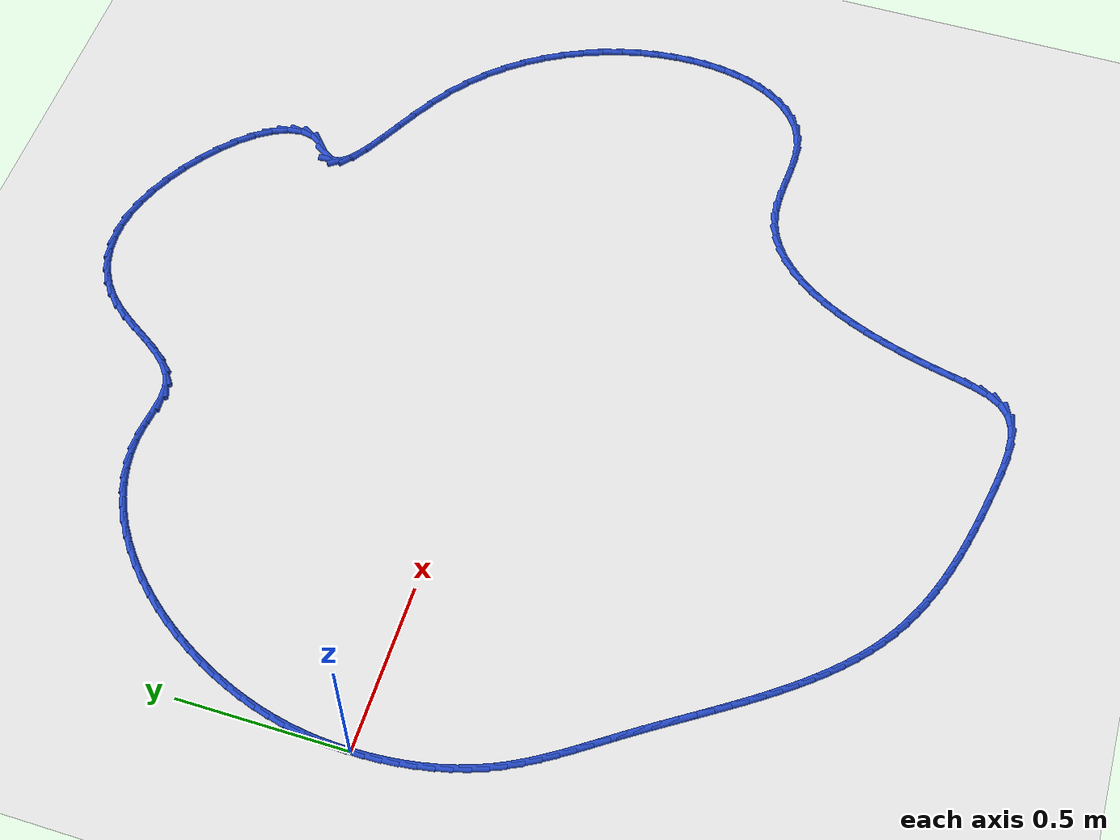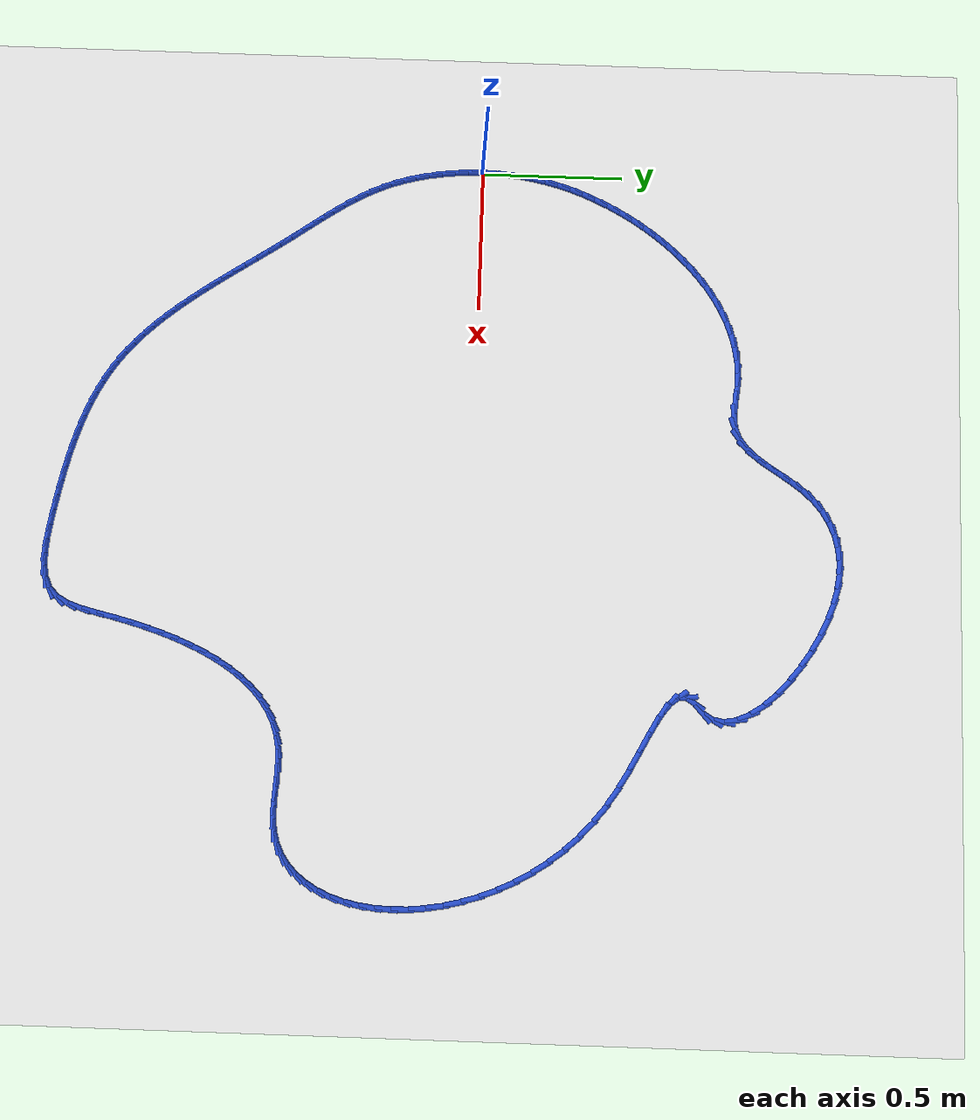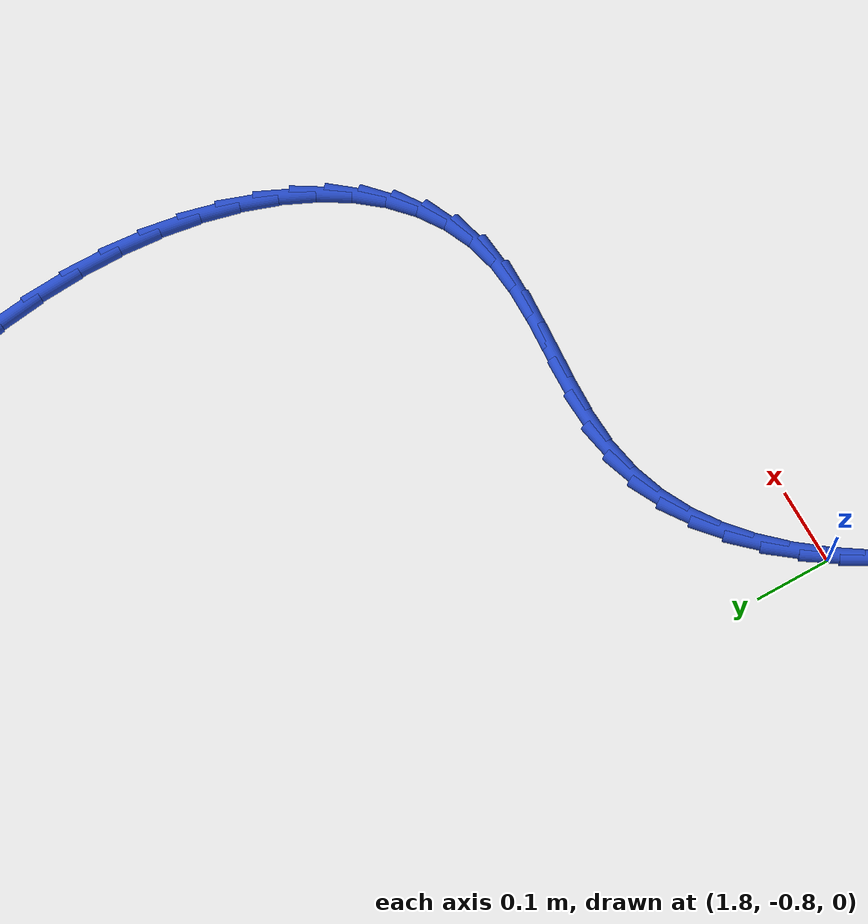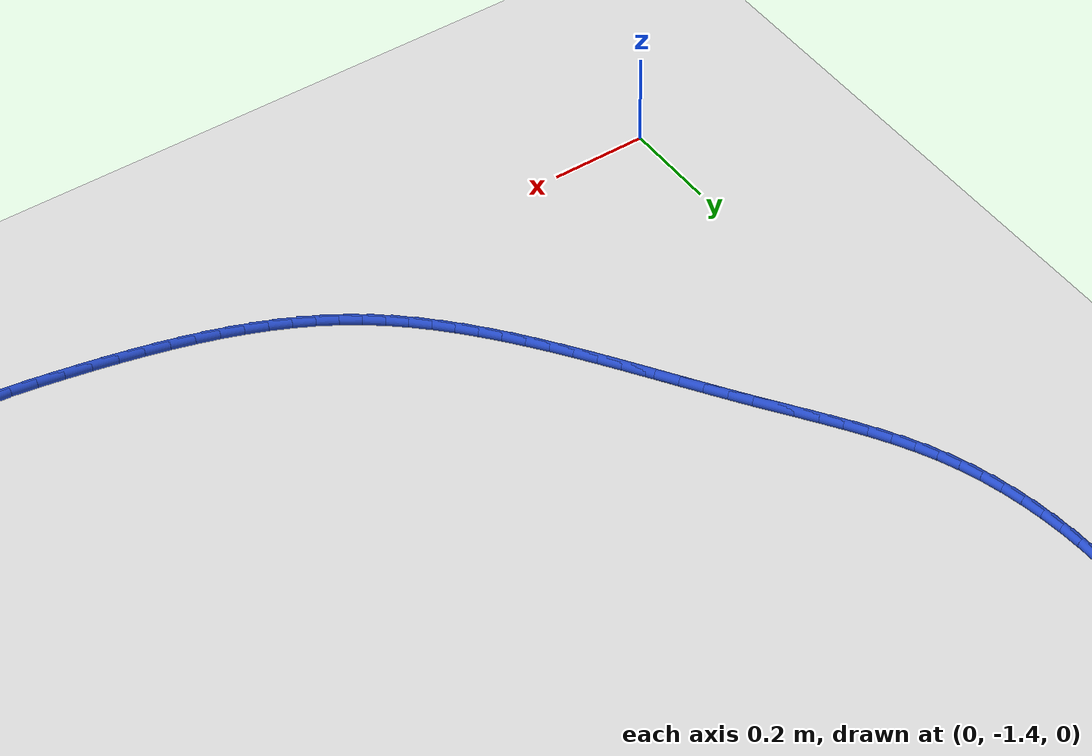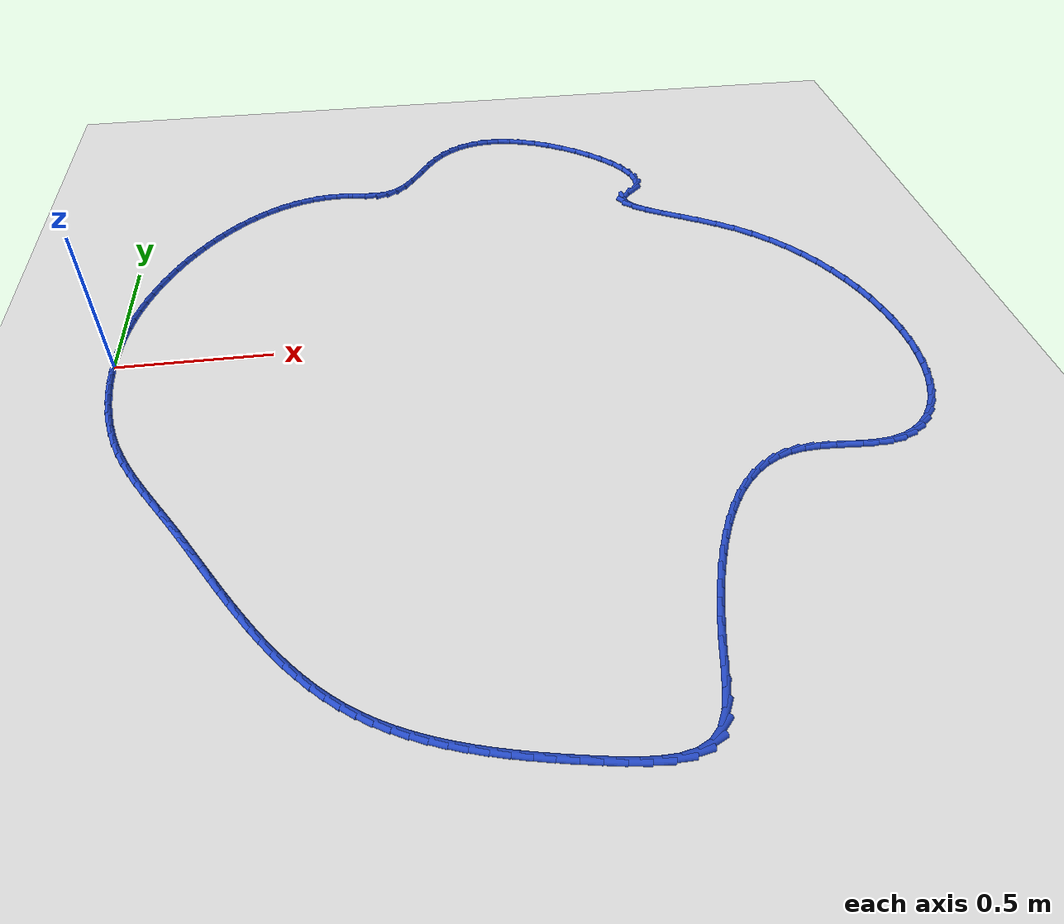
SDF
<sdf version="1.6">
 <world name="default">
  <light name="sun" type="directional">
   <pose>0 0 10 0 -0 0</pose>
   <diffuse>0.8 0.8 0.8 1</diffuse>
   <specular>0.2 0.2 0.2 1</specular>
   <attenuation>
    <range>1000</range>
    <constant>0.9</constant>
    <linear>0.01</linear>
    <quadratic>0.001</quadratic>
   </attenuation>
   <direction>-0.5 0.1 -0.9</direction>
  </light>
  <model name="ground_plane">
   <static>1</static>
   <link name="link">
    <collision name="collision">
     <geometry><plane><normal>0 0 1</normal><size>100 100</size></plane></geometry>
     <surface><friction><ode><mu>100</mu><mu2>50</mu2></ode></friction></surface>
    </collision>
    <visual name="visual">
     <cast_shadows>0</cast_shadows>
     <geometry><plane><normal>0 0 1</normal><size>100 100</size></plane></geometry>
     <material>
      <script><uri>file://media/materials/scripts/gazebo.material</uri><name>Gazebo/WhiteGlow</name></script>
     </material>
    </visual>
   </link>
  </model>
  <gravity>0 0 -9.8</gravity>
  <magnetic_field>6e-06 2.3e-05 -4.2e-05</magnetic_field>
  <atmosphere type="adiabatic"/>
  <physics name="default_physics" default="0" type="ode">
   <max_step_size>0.001</max_step_size>
   <real_time_factor>1</real_time_factor>
   <real_time_update_rate>1000</real_time_update_rate>
  </physics>
  <scene><ambient>0.4 0.4 0.4 1</ambient><background>0.7 0.7 0.7 1</background><shadows>1</shadows></scene>
  <spherical_coordinates>
   <surface_model>EARTH_WGS84</surface_model>
   <latitude_deg>0</latitude_deg>
   <longitude_deg>0</longitude_deg>
   <elevation>0</elevation>
   <heading_deg>0</heading_deg>
  </spherical_coordinates>
  <model name="line">
   <link name="link_0">
    <pose>-1.734723475976807e-18 1.0408340855860843e-16 0.01 0 1.57 1.5473383544883825</pose>
    <collision name="collision">
     <geometry><cylinder><radius>0.01</radius><length>0.08</length></cylinder></geometry>
    </collision>
    <visual name="visual">
     <material>
      <script><name>Gazebo/Blue</name><uri>file://media/materials/scripts/gazebo.material</uri></script>
     </material>
     <geometry><cylinder><radius>0.01</radius><length>0.08</length></cylinder></geometry>
    </visual>
   </link>
   <link name="link_1">
    <pose>0.001089594265778912 0.04644026281776997 0.01 0 1.57 1.5030457825430155</pose>
    <collision name="collision">
     <geometry><cylinder><radius>0.01</radius><length>0.08</length></cylinder></geometry>
    </collision>
    <visual name="visual">
     <material>
      <script><name>Gazebo/Blue</name><uri>file://media/materials/scripts/gazebo.material</uri></script>
     </material>
     <geometry><cylinder><radius>0.01</radius><length>0.08</length></cylinder></geometry>
    </visual>
   </link>
   <link name="link_2">
    <pose>0.004218759372297732 0.09255614145097091 0.01 0 1.57 1.4571612512734187</pose>
    <collision name="collision">
     <geometry><cylinder><radius>0.01</radius><length>0.08</length></cylinder></geometry>
    </collision>
    <visual name="visual">
     <material>
      <script><name>Gazebo/Blue</name><uri>file://media/materials/scripts/gazebo.material</uri></script>
     </material>
     <geometry><cylinder><radius>0.01</radius><length>0.08</length></cylinder></geometry>
    </visual>
   </link>
   <link name="link_3">
    <pose>0.0094524364315779 0.13841460768023775 0.01 0 1.57 1.4100868340457353</pose>
    <collision name="collision">
     <geometry><cylinder><radius>0.01</radius><length>0.08</length></cylinder></geometry>
    </collision>
    <visual name="visual">
     <material>
      <script><name>Gazebo/Blue</name><uri>file://media/materials/scripts/gazebo.material</uri></script>
     </material>
     <geometry><cylinder><radius>0.01</radius><length>0.08</length></cylinder></geometry>
    </visual>
   </link>
   <link name="link_4">
    <pose>0.016855566555640876 0.1840826332862054 0.01 0 1.57 1.3622659840107938</pose>
    <collision name="collision">
     <geometry><cylinder><radius>0.01</radius><length>0.08</length></cylinder></geometry>
    </collision>
    <visual name="visual">
     <material>
      <script><name>Gazebo/Blue</name><uri>file://media/materials/scripts/gazebo.material</uri></script>
     </material>
     <geometry><cylinder><radius>0.01</radius><length>0.08</length></cylinder></geometry>
    </visual>
   </link>
   <link name="link_5">
    <pose>0.02649309085650813 0.2296271900495086 0.01 0 1.57 1.3141652478452397</pose>
    <collision name="collision">
     <geometry><cylinder><radius>0.01</radius><length>0.08</length></cylinder></geometry>
    </collision>
    <visual name="visual">
     <material>
      <script><name>Gazebo/Blue</name><uri>file://media/materials/scripts/gazebo.material</uri></script>
     </material>
     <geometry><cylinder><radius>0.01</radius><length>0.08</length></cylinder></geometry>
    </visual>
   </link>
   <link name="link_6">
    <pose>0.038429950446201094 0.2751152497507822 0.01 0 1.57 1.266253507206151</pose>
    <collision name="collision">
     <geometry><cylinder><radius>0.01</radius><length>0.08</length></cylinder></geometry>
    </collision>
    <visual name="visual">
     <material>
      <script><name>Gazebo/Blue</name><uri>file://media/materials/scripts/gazebo.material</uri></script>
     </material>
     <geometry><cylinder><radius>0.01</radius><length>0.08</length></cylinder></geometry>
    </visual>
   </link>
   <link name="link_7">
    <pose>0.05273108643674122 0.3206137841706611 0.01 0 1.57 1.2189810932053469</pose>
    <collision name="collision">
     <geometry><cylinder><radius>0.01</radius><length>0.08</length></cylinder></geometry>
    </collision>
    <visual name="visual">
     <material>
      <script><name>Gazebo/Blue</name><uri>file://media/materials/scripts/gazebo.material</uri></script>
     </material>
     <geometry><cylinder><radius>0.01</radius><length>0.08</length></cylinder></geometry>
    </visual>
   </link>
   <link name="link_8">
    <pose>0.06946140719264884 0.36618968924018297 0.01 0 1.57 1.1727773760705353</pose>
    <collision name="collision">
     <geometry><cylinder><radius>0.01</radius><length>0.08</length></cylinder></geometry>
    </collision>
    <visual name="visual">
     <material>
      <script><name>Gazebo/Blue</name><uri>file://media/materials/scripts/gazebo.material</uri></script>
     </material>
     <geometry><cylinder><radius>0.01</radius><length>0.08</length></cylinder></geometry>
    </visual>
   </link>
   <link name="link_9">
    <pose>0.08865097903789822 0.41182915993174 0.01 0 1.57 1.1275881045708818</pose>
    <collision name="collision">
     <geometry><cylinder><radius>0.01</radius><length>0.08</length></cylinder></geometry>
    </collision>
    <visual name="visual">
     <material>
      <script><name>Gazebo/Blue</name><uri>file://media/materials/scripts/gazebo.material</uri></script>
     </material>
     <geometry><cylinder><radius>0.01</radius><length>0.08</length></cylinder></geometry>
    </visual>
   </link>
   <link name="link_10">
    <pose>0.11022886189254487 0.4572844406942226 0.01 0 1.57 1.0827953044987713</pose>
    <collision name="collision">
     <geometry><cylinder><radius>0.01</radius><length>0.08</length></cylinder></geometry>
    </collision>
    <visual name="visual">
     <material>
      <script><name>Gazebo/Blue</name><uri>file://media/materials/scripts/gazebo.material</uri></script>
     </material>
     <geometry><cylinder><radius>0.01</radius><length>0.08</length></cylinder></geometry>
    </visual>
   </link>
   <link name="link_11">
    <pose>0.13410591677084932 0.502265623762674 0.01 0 1.57 1.037779779084442</pose>
    <collision name="collision">
     <geometry><cylinder><radius>0.01</radius><length>0.08</length></cylinder></geometry>
    </collision>
    <visual name="visual">
     <material>
      <script><name>Gazebo/Blue</name><uri>file://media/materials/scripts/gazebo.material</uri></script>
     </material>
     <geometry><cylinder><radius>0.01</radius><length>0.08</length></cylinder></geometry>
    </visual>
   </link>
   <link name="link_12">
    <pose>0.16019300468707245 0.5464828013721387 0.01 0 1.57 0.9919517788861468</pose>
    <collision name="collision">
     <geometry><cylinder><radius>0.01</radius><length>0.08</length></cylinder></geometry>
    </collision>
    <visual name="visual">
     <material>
      <script><name>Gazebo/Blue</name><uri>file://media/materials/scripts/gazebo.material</uri></script>
     </material>
     <geometry><cylinder><radius>0.01</radius><length>0.08</length></cylinder></geometry>
    </visual>
   </link>
   <link name="link_13">
    <pose>0.1884009866554748 0.5896460657576601 0.01 0 1.57 0.9447331194122285</pose>
    <collision name="collision">
     <geometry><cylinder><radius>0.01</radius><length>0.08</length></cylinder></geometry>
    </collision>
    <visual name="visual">
     <material>
      <script><name>Gazebo/Blue</name><uri>file://media/materials/scripts/gazebo.material</uri></script>
     </material>
     <geometry><cylinder><radius>0.01</radius><length>0.08</length></cylinder></geometry>
    </visual>
   </link>
   <link name="link_14">
    <pose>0.218640723690317 0.6314655091542819 0.01 0 1.57 0.8955430141777623</pose>
    <collision name="collision">
     <geometry><cylinder><radius>0.01</radius><length>0.08</length></cylinder></geometry>
    </collision>
    <visual name="visual">
     <material>
      <script><name>Gazebo/Blue</name><uri>file://media/materials/scripts/gazebo.material</uri></script>
     </material>
     <geometry><cylinder><radius>0.01</radius><length>0.08</length></cylinder></geometry>
    </visual>
   </link>
   <link name="link_15">
    <pose>0.25082307680585975 0.6716512237970481 0.01 0 1.57 0.8437877352451366</pose>
    <collision name="collision">
     <geometry><cylinder><radius>0.01</radius><length>0.08</length></cylinder></geometry>
    </collision>
    <visual name="visual">
     <material>
      <script><name>Gazebo/Blue</name><uri>file://media/materials/scripts/gazebo.material</uri></script>
     </material>
     <geometry><cylinder><radius>0.01</radius><length>0.08</length></cylinder></geometry>
    </visual>
   </link>
   <link name="link_16">
    <pose>0.28485890701636385 0.7099133019210027 0.01 0 1.57 0.7888549346922865</pose>
    <collision name="collision">
     <geometry><cylinder><radius>0.01</radius><length>0.08</length></cylinder></geometry>
    </collision>
    <visual name="visual">
     <material>
      <script><name>Gazebo/Blue</name><uri>file://media/materials/scripts/gazebo.material</uri></script>
     </material>
     <geometry><cylinder><radius>0.01</radius><length>0.08</length></cylinder></geometry>
    </visual>
   </link>
   <link name="link_17">
    <pose>0.32065907533608984 0.7459618357611892 0.01 0 1.57 0.730114356622109</pose>
    <collision name="collision">
     <geometry><cylinder><radius>0.01</radius><length>0.08</length></cylinder></geometry>
    </collision>
    <visual name="visual">
     <material>
      <script><name>Gazebo/Blue</name><uri>file://media/materials/scripts/gazebo.material</uri></script>
     </material>
     <geometry><cylinder><radius>0.01</radius><length>0.08</length></cylinder></geometry>
    </visual>
   </link>
   <link name="link_18">
    <pose>0.35813444277929835 0.7795069175526516 0.01 0 1.57 0.6669277463735875</pose>
    <collision name="collision">
     <geometry><cylinder><radius>0.01</radius><length>0.08</length></cylinder></geometry>
    </collision>
    <visual name="visual">
     <material>
      <script><name>Gazebo/Blue</name><uri>file://media/materials/scripts/gazebo.material</uri></script>
     </material>
     <geometry><cylinder><radius>0.01</radius><length>0.08</length></cylinder></geometry>
    </visual>
   </link>
   <link name="link_19">
    <pose>0.39719587036025 0.8102586395304332 0.01 0 1.57 0.5986719058905151</pose>
    <collision name="collision">
     <geometry><cylinder><radius>0.01</radius><length>0.08</length></cylinder></geometry>
    </collision>
    <visual name="visual">
     <material>
      <script><name>Gazebo/Blue</name><uri>file://media/materials/scripts/gazebo.material</uri></script>
     </material>
     <geometry><cylinder><radius>0.01</radius><length>0.08</length></cylinder></geometry>
    </visual>
   </link>
   <link name="link_20">
    <pose>0.4377542190932057 0.8379270939295784 0.01 0 1.57 0.5247796738081281</pose>
    <collision name="collision">
     <geometry><cylinder><radius>0.01</radius><length>0.08</length></cylinder></geometry>
    </collision>
    <visual name="visual">
     <material>
      <script><name>Gazebo/Blue</name><uri>file://media/materials/scripts/gazebo.material</uri></script>
     </material>
     <geometry><cylinder><radius>0.01</radius><length>0.08</length></cylinder></geometry>
    </visual>
   </link>
   <link name="link_21">
    <pose>0.479720349992426 0.8622223729851309 0.01 0 1.57 0.44480329778574185</pose>
    <collision name="collision">
     <geometry><cylinder><radius>0.01</radius><length>0.08</length></cylinder></geometry>
    </collision>
    <visual name="visual">
     <material>
      <script><name>Gazebo/Blue</name><uri>file://media/materials/scripts/gazebo.material</uri></script>
     </material>
     <geometry><cylinder><radius>0.01</radius><length>0.08</length></cylinder></geometry>
    </visual>
   </link>
   <link name="link_22">
    <pose>0.5230051240721714 0.8828545689321343 0.01 0 1.57 0.3585018195062949</pose>
    <collision name="collision">
     <geometry><cylinder><radius>0.01</radius><length>0.08</length></cylinder></geometry>
    </collision>
    <visual name="visual">
     <material>
      <script><name>Gazebo/Blue</name><uri>file://media/materials/scripts/gazebo.material</uri></script>
     </material>
     <geometry><cylinder><radius>0.01</radius><length>0.08</length></cylinder></geometry>
    </visual>
   </link>
   <link name="link_23">
    <pose>0.567519402346703 0.8995337740056326 0.01 0 1.57 0.26594703226347116</pose>
    <collision name="collision">
     <geometry><cylinder><radius>0.01</radius><length>0.08</length></cylinder></geometry>
    </collision>
    <visual name="visual">
     <material>
      <script><name>Gazebo/Blue</name><uri>file://media/materials/scripts/gazebo.material</uri></script>
     </material>
     <geometry><cylinder><radius>0.01</radius><length>0.08</length></cylinder></geometry>
    </visual>
   </link>
   <link name="link_24">
    <pose>0.6131740458302809 0.9119700804406694 0.01 0 1.57 0.16763056884097485</pose>
    <collision name="collision">
     <geometry><cylinder><radius>0.01</radius><length>0.08</length></cylinder></geometry>
    </collision>
    <visual name="visual">
     <material>
      <script><name>Gazebo/Blue</name><uri>file://media/materials/scripts/gazebo.material</uri></script>
     </material>
     <geometry><cylinder><radius>0.01</radius><length>0.08</length></cylinder></geometry>
    </visual>
   </link>
   <link name="link_25">
    <pose>0.6598799155371664 0.9198735804722888 0.01 0 1.57 0.06454035885185302</pose>
    <collision name="collision">
     <geometry><cylinder><radius>0.01</radius><length>0.08</length></cylinder></geometry>
    </collision>
    <visual name="visual">
     <material>
      <script><name>Gazebo/Blue</name><uri>file://media/materials/scripts/gazebo.material</uri></script>
     </material>
     <geometry><cylinder><radius>0.01</radius><length>0.08</length></cylinder></geometry>
    </visual>
   </link>
   <link name="link_26">
    <pose>0.7075478724816195 0.922954366335534 0.01 0 1.57 -0.04161294874814246</pose>
    <collision name="collision">
     <geometry><cylinder><radius>0.01</radius><length>0.08</length></cylinder></geometry>
    </collision>
    <visual name="visual">
     <material>
      <script><name>Gazebo/Blue</name><uri>file://media/materials/scripts/gazebo.material</uri></script>
     </material>
     <geometry><cylinder><radius>0.01</radius><length>0.08</length></cylinder></geometry>
    </visual>
   </link>
   <link name="link_27">
    <pose>0.7560852770717118 0.9209334151529838 0.01 0 1.57 -0.11482870221932892</pose>
    <collision name="collision">
     <geometry><cylinder><radius>0.01</radius><length>0.08</length></cylinder></geometry>
    </collision>
    <visual name="visual">
     <material>
      <script><name>Gazebo/Blue</name><uri>file://media/materials/scripts/gazebo.material</uri></script>
     </material>
     <geometry><cylinder><radius>0.01</radius><length>0.08</length></cylinder></geometry>
    </visual>
   </link>
   <link name="link_28">
    <pose>0.8048270281217221 0.9153117329133174 0.01 0 1.57 -0.08438538848249325</pose>
    <collision name="collision">
     <geometry><cylinder><radius>0.01</radius><length>0.08</length></cylinder></geometry>
    </collision>
    <visual name="visual">
     <material>
      <script><name>Gazebo/Blue</name><uri>file://media/materials/scripts/gazebo.material</uri></script>
     </material>
     <geometry><cylinder><radius>0.01</radius><length>0.08</length></cylinder></geometry>
    </visual>
   </link>
   <link name="link_29">
    <pose>0.8519054832552916 0.9113295424456483 0.01 0 1.57 0.07748621107274571</pose>
    <collision name="collision">
     <geometry><cylinder><radius>0.01</radius><length>0.08</length></cylinder></geometry>
    </collision>
    <visual name="visual">
     <material>
      <script><name>Gazebo/Blue</name><uri>file://media/materials/scripts/gazebo.material</uri></script>
     </material>
     <geometry><cylinder><radius>0.01</radius><length>0.08</length></cylinder></geometry>
    </visual>
   </link>
   <link name="link_30">
    <pose>0.8953012690869138 0.9146988634281619 0.01 0 1.57 0.3780868927722945</pose>
    <collision name="collision">
     <geometry><cylinder><radius>0.01</radius><length>0.08</length></cylinder></geometry>
    </collision>
    <visual name="visual">
     <material>
      <script><name>Gazebo/Blue</name><uri>file://media/materials/scripts/gazebo.material</uri></script>
     </material>
     <geometry><cylinder><radius>0.01</radius><length>0.08</length></cylinder></geometry>
    </visual>
   </link>
   <link name="link_31">
    <pose>0.9334954465727384 0.9298694420082915 0.01 0 1.57 0.6559467484666813</pose>
    <collision name="collision">
     <geometry><cylinder><radius>0.01</radius><length>0.08</length></cylinder></geometry>
    </collision>
    <visual name="visual">
     <material>
      <script><name>Gazebo/Blue</name><uri>file://media/materials/scripts/gazebo.material</uri></script>
     </material>
     <geometry><cylinder><radius>0.01</radius><length>0.08</length></cylinder></geometry>
    </visual>
   </link>
   <link name="link_32">
    <pose>0.9671557547510595 0.9557754438994175 0.01 0 1.57 0.8423977463634394</pose>
    <collision name="collision">
     <geometry><cylinder><radius>0.01</radius><length>0.08</length></cylinder></geometry>
    </collision>
    <visual name="visual">
     <material>
      <script><name>Gazebo/Blue</name><uri>file://media/materials/scripts/gazebo.material</uri></script>
     </material>
     <geometry><cylinder><radius>0.01</radius><length>0.08</length></cylinder></geometry>
    </visual>
   </link>
   <link name="link_33">
    <pose>0.9975470306072215 0.9898449412655947 0.01 0 1.57 0.9495827120929485</pose>
    <collision name="collision">
     <geometry><cylinder><radius>0.01</radius><length>0.08</length></cylinder></geometry>
    </collision>
    <visual name="visual">
     <material>
      <script><name>Gazebo/Blue</name><uri>file://media/materials/scripts/gazebo.material</uri></script>
     </material>
     <geometry><cylinder><radius>0.01</radius><length>0.08</length></cylinder></geometry>
    </visual>
   </link>
   <link name="link_34">
    <pose>1.0259341250950313 1.0295059710374463 0.01 0 1.57 0.9959812496932988</pose>
    <collision name="collision">
     <geometry><cylinder><radius>0.01</radius><length>0.08</length></cylinder></geometry>
    </collision>
    <visual name="visual">
     <material>
      <script><name>Gazebo/Blue</name><uri>file://media/materials/scripts/gazebo.material</uri></script>
     </material>
     <geometry><cylinder><radius>0.01</radius><length>0.08</length></cylinder></geometry>
    </visual>
   </link>
   <link name="link_35">
    <pose>1.0535818891682955 1.0721865701455955 0.01 0 1.57 0.9921432910593081</pose>
    <collision name="collision">
     <geometry><cylinder><radius>0.01</radius><length>0.08</length></cylinder></geometry>
    </collision>
    <visual name="visual">
     <material>
      <script><name>Gazebo/Blue</name><uri>file://media/materials/scripts/gazebo.material</uri></script>
     </material>
     <geometry><cylinder><radius>0.01</radius><length>0.08</length></cylinder></geometry>
    </visual>
   </link>
   <link name="link_36">
    <pose>1.0817551737808204 1.1153147755206647 0.01 0 1.57 0.9397279849570357</pose>
    <collision name="collision">
     <geometry><cylinder><radius>0.01</radius><length>0.08</length></cylinder></geometry>
    </collision>
    <visual name="visual">
     <material>
      <script><name>Gazebo/Blue</name><uri>file://media/materials/scripts/gazebo.material</uri></script>
     </material>
     <geometry><cylinder><radius>0.01</radius><length>0.08</length></cylinder></geometry>
    </visual>
   </link>
   <link name="link_37">
    <pose>1.1117188298864131 1.1563186240932772 0.01 0 1.57 0.8347586795625872</pose>
    <collision name="collision">
     <geometry><cylinder><radius>0.01</radius><length>0.08</length></cylinder></geometry>
    </collision>
    <visual name="visual">
     <material>
      <script><name>Gazebo/Blue</name><uri>file://media/materials/scripts/gazebo.material</uri></script>
     </material>
     <geometry><cylinder><radius>0.01</radius><length>0.08</length></cylinder></geometry>
    </visual>
   </link>
   <link name="link_38">
    <pose>1.1446857114057727 1.1927119442131495 0.01 0 1.57 0.6986438046717055</pose>
    <collision name="collision">
     <geometry><cylinder><radius>0.01</radius><length>0.08</length></cylinder></geometry>
    </collision>
    <visual name="visual">
     <material>
      <script><name>Gazebo/Blue</name><uri>file://media/materials/scripts/gazebo.material</uri></script>
     </material>
     <geometry><cylinder><radius>0.01</radius><length>0.08</length></cylinder></geometry>
    </visual>
   </link>
   <link name="link_39">
    <pose>1.1810911110173015 1.2232914851664756 0.01 0 1.57 0.5540406453895251</pose>
    <collision name="collision">
     <geometry><cylinder><radius>0.01</radius><length>0.08</length></cylinder></geometry>
    </collision>
    <visual name="visual">
     <material>
      <script><name>Gazebo/Blue</name><uri>file://media/materials/scripts/gazebo.material</uri></script>
     </material>
     <geometry><cylinder><radius>0.01</radius><length>0.08</length></cylinder></geometry>
    </visual>
   </link>
   <link name="link_40">
    <pose>1.220771992706759 1.2478411961729523 0.01 0 1.57 0.40480872486395214</pose>
    <collision name="collision">
     <geometry><cylinder><radius>0.01</radius><length>0.08</length></cylinder></geometry>
    </collision>
    <visual name="visual">
     <material>
      <script><name>Gazebo/Blue</name><uri>file://media/materials/scripts/gazebo.material</uri></script>
     </material>
     <geometry><cylinder><radius>0.01</radius><length>0.08</length></cylinder></geometry>
    </visual>
   </link>
   <link name="link_41">
    <pose>1.2635499431950588 1.2661703978493364 0.01 0 1.57 0.25512418469562126</pose>
    <collision name="collision">
     <geometry><cylinder><radius>0.01</radius><length>0.08</length></cylinder></geometry>
    </collision>
    <visual name="visual">
     <material>
      <script><name>Gazebo/Blue</name><uri>file://media/materials/scripts/gazebo.material</uri></script>
     </material>
     <geometry><cylinder><radius>0.01</radius><length>0.08</length></cylinder></geometry>
    </visual>
   </link>
   <link name="link_42">
    <pose>1.3092465492031138 1.278088410812385 0.01 0 1.57 0.10931660457676289</pose>
    <collision name="collision">
     <geometry><cylinder><radius>0.01</radius><length>0.08</length></cylinder></geometry>
    </collision>
    <visual name="visual">
     <material>
      <script><name>Gazebo/Blue</name><uri>file://media/materials/scripts/gazebo.material</uri></script>
     </material>
     <geometry><cylinder><radius>0.01</radius><length>0.08</length></cylinder></geometry>
    </visual>
   </link>
   <link name="link_43">
    <pose>1.3576833974518372 1.283404555678854 0.01 0 1.57 -0.028941738247848084</pose>
    <collision name="collision">
     <geometry><cylinder><radius>0.01</radius><length>0.08</length></cylinder></geometry>
    </collision>
    <visual name="visual">
     <material>
      <script><name>Gazebo/Blue</name><uri>file://media/materials/scripts/gazebo.material</uri></script>
     </material>
     <geometry><cylinder><radius>0.01</radius><length>0.08</length></cylinder></geometry>
    </visual>
   </link>
   <link name="link_44">
    <pose>1.408682074662142 1.2819281530655002 0.01 0 1.57 -0.15716618969718724</pose>
    <collision name="collision">
     <geometry><cylinder><radius>0.01</radius><length>0.08</length></cylinder></geometry>
    </collision>
    <visual name="visual">
     <material>
      <script><name>Gazebo/Blue</name><uri>file://media/materials/scripts/gazebo.material</uri></script>
     </material>
     <geometry><cylinder><radius>0.01</radius><length>0.08</length></cylinder></geometry>
    </visual>
   </link>
   <link name="link_45">
    <pose>1.4620641675549433 1.2734685235890806 0.01 0 1.57 -0.2738550529248303</pose>
    <collision name="collision">
     <geometry><cylinder><radius>0.01</radius><length>0.08</length></cylinder></geometry>
    </collision>
    <visual name="visual">
     <material>
      <script><name>Gazebo/Blue</name><uri>file://media/materials/scripts/gazebo.material</uri></script>
     </material>
     <geometry><cylinder><radius>0.01</radius><length>0.08</length></cylinder></geometry>
    </visual>
   </link>
   <link name="link_46">
    <pose>1.5176229147134406 1.257861353680724 0.01 0 1.57 -0.3742647170377452</pose>
    <collision name="collision">
     <geometry><cylinder><radius>0.01</radius><length>0.08</length></cylinder></geometry>
    </collision>
    <visual name="visual">
     <material>
      <script><name>Gazebo/Blue</name><uri>file://media/materials/scripts/gazebo.material</uri></script>
     </material>
     <geometry><cylinder><radius>0.01</radius><length>0.08</length></cylinder></geometry>
    </visual>
   </link>
   <link name="link_47">
    <pose>1.5745502792581543 1.23550155935475 0.01 0 1.57 -0.45979591747731413</pose>
    <collision name="collision">
     <geometry><cylinder><radius>0.01</radius><length>0.08</length></cylinder></geometry>
    </collision>
    <visual name="visual">
     <material>
      <script><name>Gazebo/Blue</name><uri>file://media/materials/scripts/gazebo.material</uri></script>
     </material>
     <geometry><cylinder><radius>0.01</radius><length>0.08</length></cylinder></geometry>
    </visual>
   </link>
   <link name="link_48">
    <pose>1.631463851525005 1.207318264776078 0.01 0 1.57 -0.5372290545528736</pose>
    <collision name="collision">
     <geometry><cylinder><radius>0.01</radius><length>0.08</length></cylinder></geometry>
    </collision>
    <visual name="visual">
     <material>
      <script><name>Gazebo/Blue</name><uri>file://media/materials/scripts/gazebo.material</uri></script>
     </material>
     <geometry><cylinder><radius>0.01</radius><length>0.08</length></cylinder></geometry>
    </visual>
   </link>
   <link name="link_49">
    <pose>1.6869582577822209 1.1742619523502424 0.01 0 1.57 -0.6121255080288873</pose>
    <collision name="collision">
     <geometry><cylinder><radius>0.01</radius><length>0.08</length></cylinder></geometry>
    </collision>
    <visual name="visual">
     <material>
      <script><name>Gazebo/Blue</name><uri>file://media/materials/scripts/gazebo.material</uri></script>
     </material>
     <geometry><cylinder><radius>0.01</radius><length>0.08</length></cylinder></geometry>
    </visual>
   </link>
   <link name="link_50">
    <pose>1.7396281242980278 1.1372831044827763 0.01 0 1.57 -0.6896518820978307</pose>
    <collision name="collision">
     <geometry><cylinder><radius>0.01</radius><length>0.08</length></cylinder></geometry>
    </collision>
    <visual name="visual">
     <material>
      <script><name>Gazebo/Blue</name><uri>file://media/materials/scripts/gazebo.material</uri></script>
     </material>
     <geometry><cylinder><radius>0.01</radius><length>0.08</length></cylinder></geometry>
    </visual>
   </link>
   <link name="link_51">
    <pose>1.788068077340651 1.0973322035792132 0.01 0 1.57 -0.7755822200771194</pose>
    <collision name="collision">
     <geometry><cylinder><radius>0.01</radius><length>0.08</length></cylinder></geometry>
    </collision>
    <visual name="visual">
     <material>
      <script><name>Gazebo/Blue</name><uri>file://media/materials/scripts/gazebo.material</uri></script>
     </material>
     <geometry><cylinder><radius>0.01</radius><length>0.08</length></cylinder></geometry>
    </visual>
   </link>
   <link name="link_52">
    <pose>1.8308727431783183 1.055359732045087 0.01 0 1.57 -0.877508052750104</pose>
    <collision name="collision">
     <geometry><cylinder><radius>0.01</radius><length>0.08</length></cylinder></geometry>
    </collision>
    <visual name="visual">
     <material>
      <script><name>Gazebo/Blue</name><uri>file://media/materials/scripts/gazebo.material</uri></script>
     </material>
     <geometry><cylinder><radius>0.01</radius><length>0.08</length></cylinder></geometry>
    </visual>
   </link>
   <link name="link_53">
    <pose>1.866636748079254 1.012316172285931 0.01 0 1.57 -1.0065466959410987</pose>
    <collision name="collision">
     <geometry><cylinder><radius>0.01</radius><length>0.08</length></cylinder></geometry>
    </collision>
    <visual name="visual">
     <material>
      <script><name>Gazebo/Blue</name><uri>file://media/materials/scripts/gazebo.material</uri></script>
     </material>
     <geometry><cylinder><radius>0.01</radius><length>0.08</length></cylinder></geometry>
    </visual>
   </link>
   <link name="link_54">
    <pose>1.8939547183116852 0.9691520067072793 0.01 0 1.57 -1.1794867129779139</pose>
    <collision name="collision">
     <geometry><cylinder><radius>0.01</radius><length>0.08</length></cylinder></geometry>
    </collision>
    <visual name="visual">
     <material>
      <script><name>Gazebo/Blue</name><uri>file://media/materials/scripts/gazebo.material</uri></script>
     </material>
     <geometry><cylinder><radius>0.01</radius><length>0.08</length></cylinder></geometry>
    </visual>
   </link>
   <link name="link_55">
    <pose>1.911421280143838 0.9268177177146641 0.01 0 1.57 -1.418852538185806</pose>
    <collision name="collision">
     <geometry><cylinder><radius>0.01</radius><length>0.08</length></cylinder></geometry>
    </collision>
    <visual name="visual">
     <material>
      <script><name>Gazebo/Blue</name><uri>file://media/materials/scripts/gazebo.material</uri></script>
     </material>
     <geometry><cylinder><radius>0.01</radius><length>0.08</length></cylinder></geometry>
    </visual>
   </link>
   <link name="link_56">
    <pose>1.9176310598439388 0.8862637877136208 0.01 0 1.57 1.4018293170558438</pose>
    <collision name="collision">
     <geometry><cylinder><radius>0.01</radius><length>0.08</length></cylinder></geometry>
    </collision>
    <visual name="visual">
     <material>
      <script><name>Gazebo/Blue</name><uri>file://media/materials/scripts/gazebo.material</uri></script>
     </material>
     <geometry><cylinder><radius>0.01</radius><length>0.08</length></cylinder></geometry>
    </visual>
   </link>
   <link name="link_57">
    <pose>1.9111786836802134 0.848440699109682 0.01 0 1.57 1.0296266846451025</pose>
    <collision name="collision">
     <geometry><cylinder><radius>0.01</radius><length>0.08</length></cylinder></geometry>
    </collision>
    <visual name="visual">
     <material>
      <script><name>Gazebo/Blue</name><uri>file://media/materials/scripts/gazebo.material</uri></script>
     </material>
     <geometry><cylinder><radius>0.01</radius><length>0.08</length></cylinder></geometry>
    </visual>
   </link>
   <link name="link_58">
    <pose>1.8906587779208883 0.8142989343083809 0.01 0 1.57 0.7320176689935225</pose>
    <collision name="collision">
     <geometry><cylinder><radius>0.01</radius><length>0.08</length></cylinder></geometry>
    </collision>
    <visual name="visual">
     <material>
      <script><name>Gazebo/Blue</name><uri>file://media/materials/scripts/gazebo.material</uri></script>
     </material>
     <geometry><cylinder><radius>0.01</radius><length>0.08</length></cylinder></geometry>
    </visual>
   </link>
   <link name="link_59">
    <pose>1.857509855114538 0.7845127150880845 0.01 0 1.57 0.9939674138368683</pose>
    <collision name="collision">
     <geometry><cylinder><radius>0.01</radius><length>0.08</length></cylinder></geometry>
    </collision>
    <visual name="visual">
     <material>
      <script><name>Gazebo/Blue</name><uri>file://media/materials/scripts/gazebo.material</uri></script>
     </material>
     <geometry><cylinder><radius>0.01</radius><length>0.08</length></cylinder></geometry>
    </visual>
   </link>
   <link name="link_60">
    <pose>1.8394296436210553 0.7567246037293542 0.01 0 1.57 -1.4835059076597954</pose>
    <collision name="collision">
     <geometry><cylinder><radius>0.01</radius><length>0.08</length></cylinder></geometry>
    </collision>
    <visual name="visual">
     <material>
      <script><name>Gazebo/Blue</name><uri>file://media/materials/scripts/gazebo.material</uri></script>
     </material>
     <geometry><cylinder><radius>0.01</radius><length>0.08</length></cylinder></geometry>
    </visual>
   </link>
   <link name="link_61">
    <pose>1.8417955072330823 0.7296901182837572 0.01 0 1.57 -0.9347552738750693</pose>
    <collision name="collision">
     <geometry><cylinder><radius>0.01</radius><length>0.08</length></cylinder></geometry>
    </collision>
    <visual name="visual">
     <material>
      <script><name>Gazebo/Blue</name><uri>file://media/materials/scripts/gazebo.material</uri></script>
     </material>
     <geometry><cylinder><radius>0.01</radius><length>0.08</length></cylinder></geometry>
    </visual>
   </link>
   <link name="link_62">
    <pose>1.8616177484712118 0.7028455647499979 0.01 0 1.57 -0.670944886288404</pose>
    <collision name="collision">
     <geometry><cylinder><radius>0.01</radius><length>0.08</length></cylinder></geometry>
    </collision>
    <visual name="visual">
     <material>
      <script><name>Gazebo/Blue</name><uri>file://media/materials/scripts/gazebo.material</uri></script>
     </material>
     <geometry><cylinder><radius>0.01</radius><length>0.08</length></cylinder></geometry>
    </visual>
   </link>
   <link name="link_63">
    <pose>1.8959066698560367 0.6756272491267801 0.01 0 1.57 -0.5515303790536388</pose>
    <collision name="collision">
     <geometry><cylinder><radius>0.01</radius><length>0.08</length></cylinder></geometry>
    </collision>
    <visual name="visual">
     <material>
      <script><name>Gazebo/Blue</name><uri>file://media/materials/scripts/gazebo.material</uri></script>
     </material>
     <geometry><cylinder><radius>0.01</radius><length>0.08</length></cylinder></geometry>
    </visual>
   </link>
   <link name="link_64">
    <pose>1.9416725739081506 0.647471477412809 0.01 0 1.57 -0.5002593071246048</pose>
    <collision name="collision">
     <geometry><cylinder><radius>0.01</radius><length>0.08</length></cylinder></geometry>
    </collision>
    <visual name="visual">
     <material>
      <script><name>Gazebo/Blue</name><uri>file://media/materials/scripts/gazebo.material</uri></script>
     </material>
     <geometry><cylinder><radius>0.01</radius><length>0.08</length></cylinder></geometry>
    </visual>
   </link>
   <link name="link_65">
    <pose>1.9959257631481455 0.6178145556067881 0.01 0 1.57 -0.48806197262878614</pose>
    <collision name="collision">
     <geometry><cylinder><radius>0.01</radius><length>0.08</length></cylinder></geometry>
    </collision>
    <visual name="visual">
     <material>
      <script><name>Gazebo/Blue</name><uri>file://media/materials/scripts/gazebo.material</uri></script>
     </material>
     <geometry><cylinder><radius>0.01</radius><length>0.08</length></cylinder></geometry>
    </visual>
   </link>
   <link name="link_66">
    <pose>2.055676540096615 0.5860927897074215 0.01 0 1.57 -0.5041745135289533</pose>
    <collision name="collision">
     <geometry><cylinder><radius>0.01</radius><length>0.08</length></cylinder></geometry>
    </collision>
    <visual name="visual">
     <material>
      <script><name>Gazebo/Blue</name><uri>file://media/materials/scripts/gazebo.material</uri></script>
     </material>
     <geometry><cylinder><radius>0.01</radius><length>0.08</length></cylinder></geometry>
    </visual>
   </link>
   <link name="link_67">
    <pose>2.117935207274152 0.5517424857134144 0.01 0 1.57 -0.5460707648363307</pose>
    <collision name="collision">
     <geometry><cylinder><radius>0.01</radius><length>0.08</length></cylinder></geometry>
    </collision>
    <visual name="visual">
     <material>
      <script><name>Gazebo/Blue</name><uri>file://media/materials/scripts/gazebo.material</uri></script>
     </material>
     <geometry><cylinder><radius>0.01</radius><length>0.08</length></cylinder></geometry>
    </visual>
   </link>
   <link name="link_68">
    <pose>2.1797120672013506 0.5141999496234702 0.01 0 1.57 -0.6153120141274016</pose>
    <collision name="collision">
     <geometry><cylinder><radius>0.01</radius><length>0.08</length></cylinder></geometry>
    </collision>
    <visual name="visual">
     <material>
      <script><name>Gazebo/Blue</name><uri>file://media/materials/scripts/gazebo.material</uri></script>
     </material>
     <geometry><cylinder><radius>0.01</radius><length>0.08</length></cylinder></geometry>
    </visual>
   </link>
   <link name="link_69">
    <pose>2.2380994836153865 0.4729284966766146 0.01 0 1.57 -0.6984010794352226</pose>
    <collision name="collision">
     <geometry><cylinder><radius>0.01</radius><length>0.08</length></cylinder></geometry>
    </collision>
    <visual name="visual">
     <material>
      <script><name>Gazebo/Blue</name><uri>file://media/materials/scripts/gazebo.material</uri></script>
     </material>
     <geometry><cylinder><radius>0.01</radius><length>0.08</length></cylinder></geometry>
    </visual>
   </link>
   <link name="link_70">
    <pose>2.2917335562703327 0.4278995400758916 0.01 0 1.57 -0.7799694001548735</pose>
    <collision name="collision">
     <geometry><cylinder><radius>0.01</radius><length>0.08</length></cylinder></geometry>
    </collision>
    <visual name="visual">
     <material>
      <script><name>Gazebo/Blue</name><uri>file://media/materials/scripts/gazebo.material</uri></script>
     </material>
     <geometry><cylinder><radius>0.01</radius><length>0.08</length></cylinder></geometry>
    </visual>
   </link>
   <link name="link_71">
    <pose>2.3406243537924114 0.3795367146340812 0.01 0 1.57 -0.8591329846517987</pose>
    <collision name="collision">
     <geometry><cylinder><radius>0.01</radius><length>0.08</length></cylinder></geometry>
    </collision>
    <visual name="visual">
     <material>
      <script><name>Gazebo/Blue</name><uri>file://media/materials/scripts/gazebo.material</uri></script>
     </material>
     <geometry><cylinder><radius>0.01</radius><length>0.08</length></cylinder></geometry>
    </visual>
   </link>
   <link name="link_72">
    <pose>2.384829908066514 0.3282794415638477 0.01 0 1.57 -0.9357592254771411</pose>
    <collision name="collision">
     <geometry><cylinder><radius>0.01</radius><length>0.08</length></cylinder></geometry>
    </collision>
    <visual name="visual">
     <material>
      <script><name>Gazebo/Blue</name><uri>file://media/materials/scripts/gazebo.material</uri></script>
     </material>
     <geometry><cylinder><radius>0.01</radius><length>0.08</length></cylinder></geometry>
    </visual>
   </link>
   <link name="link_73">
    <pose>2.424408250977531 0.27456714207785443 0.01 0 1.57 -1.0098876976635547</pose>
    <collision name="collision">
     <geometry><cylinder><radius>0.01</radius><length>0.08</length></cylinder></geometry>
    </collision>
    <visual name="visual">
     <material>
      <script><name>Gazebo/Blue</name><uri>file://media/materials/scripts/gazebo.material</uri></script>
     </material>
     <geometry><cylinder><radius>0.01</radius><length>0.08</length></cylinder></geometry>
    </visual>
   </link>
   <link name="link_74">
    <pose>2.4594174144103533 0.21883923738876418 0.01 0 1.57 -1.081711163616409</pose>
    <collision name="collision">
     <geometry><cylinder><radius>0.01</radius><length>0.08</length></cylinder></geometry>
    </collision>
    <visual name="visual">
     <material>
      <script><name>Gazebo/Blue</name><uri>file://media/materials/scripts/gazebo.material</uri></script>
     </material>
     <geometry><cylinder><radius>0.01</radius><length>0.08</length></cylinder></geometry>
    </visual>
   </link>
   <link name="link_75">
    <pose>2.4899154302498716 0.16153514870924163 0.01 0 1.57 -1.1515552584833622</pose>
    <collision name="collision">
     <geometry><cylinder><radius>0.01</radius><length>0.08</length></cylinder></geometry>
    </collision>
    <visual name="visual">
     <material>
      <script><name>Gazebo/Blue</name><uri>file://media/materials/scripts/gazebo.material</uri></script>
     </material>
     <geometry><cylinder><radius>0.01</radius><length>0.08</length></cylinder></geometry>
    </visual>
   </link>
   <link name="link_76">
    <pose>2.515960330380976 0.1030942972519499 0.01 0 1.57 -1.2198612167874734</pose>
    <collision name="collision">
     <geometry><cylinder><radius>0.01</radius><length>0.08</length></cylinder></geometry>
    </collision>
    <visual name="visual">
     <material>
      <script><name>Gazebo/Blue</name><uri>file://media/materials/scripts/gazebo.material</uri></script>
     </material>
     <geometry><cylinder><radius>0.01</radius><length>0.08</length></cylinder></geometry>
    </visual>
   </link>
   <link name="link_77">
    <pose>2.537610146688558 0.043956104229551846 0.01 0 1.57 -1.2871744872207318</pose>
    <collision name="collision">
     <geometry><cylinder><radius>0.01</radius><length>0.08</length></cylinder></geometry>
    </collision>
    <visual name="visual">
     <material>
      <script><name>Gazebo/Blue</name><uri>file://media/materials/scripts/gazebo.material</uri></script>
     </material>
     <geometry><cylinder><radius>0.01</radius><length>0.08</length></cylinder></geometry>
    </visual>
   </link>
   <link name="link_78">
    <pose>2.5549229110575093 -0.015440009145287821 0.01 0 1.57 -1.354140845468903</pose>
    <collision name="collision">
     <geometry><cylinder><radius>0.01</radius><length>0.08</length></cylinder></geometry>
    </collision>
    <visual name="visual">
     <material>
      <script><name>Gazebo/Blue</name><uri>file://media/materials/scripts/gazebo.material</uri></script>
     </material>
     <geometry><cylinder><radius>0.01</radius><length>0.08</length></cylinder></geometry>
    </visual>
   </link>
   <link name="link_79">
    <pose>2.5679566553727184 -0.07465462165990668 0.01 0 1.57 -1.4215107797532878</pose>
    <collision name="collision">
     <geometry><cylinder><radius>0.01</radius><length>0.08</length></cylinder></geometry>
    </collision>
    <visual name="visual">
     <material>
      <script><name>Gazebo/Blue</name><uri>file://media/materials/scripts/gazebo.material</uri></script>
     </material>
     <geometry><cylinder><radius>0.01</radius><length>0.08</length></cylinder></geometry>
    </visual>
   </link>
   <link name="link_80">
    <pose>2.576769411519078 -0.13324831210163995 0.01 0 1.57 -1.490152390474565</pose>
    <collision name="collision">
     <geometry><cylinder><radius>0.01</radius><length>0.08</length></cylinder></geometry>
    </collision>
    <visual name="visual">
     <material>
      <script><name>Gazebo/Blue</name><uri>file://media/materials/scripts/gazebo.material</uri></script>
     </material>
     <geometry><cylinder><radius>0.01</radius><length>0.08</length></cylinder></geometry>
    </visual>
   </link>
   <link name="link_81">
    <pose>2.581419211381479 -0.19078165925782484 0.01 0 1.57 -1.5610725457270038</pose>
    <collision name="collision">
     <geometry><cylinder><radius>0.01</radius><length>0.08</length></cylinder></geometry>
    </collision>
    <visual name="visual">
     <material>
      <script><name>Gazebo/Blue</name><uri>file://media/materials/scripts/gazebo.material</uri></script>
     </material>
     <geometry><cylinder><radius>0.01</radius><length>0.08</length></cylinder></geometry>
    </visual>
   </link>
   <link name="link_82">
    <pose>2.5819640868448097 -0.24681524191579807 0.01 0 1.57 1.5061475454830733</pose>
    <collision name="collision">
     <geometry><cylinder><radius>0.01</radius><length>0.08</length></cylinder></geometry>
    </collision>
    <visual name="visual">
     <material>
      <script><name>Gazebo/Blue</name><uri>file://media/materials/scripts/gazebo.material</uri></script>
     </material>
     <geometry><cylinder><radius>0.01</radius><length>0.08</length></cylinder></geometry>
    </visual>
   </link>
   <link name="link_83">
    <pose>2.578462069793964 -0.30090963886289535 0.01 0 1.57 1.4269497455868427</pose>
    <collision name="collision">
     <geometry><cylinder><radius>0.01</radius><length>0.08</length></cylinder></geometry>
    </collision>
    <visual name="visual">
     <material>
      <script><name>Gazebo/Blue</name><uri>file://media/materials/scripts/gazebo.material</uri></script>
     </material>
     <geometry><cylinder><radius>0.01</radius><length>0.08</length></cylinder></geometry>
    </visual>
   </link>
   <link name="link_84">
    <pose>2.5709711921138307 -0.352625428886454 0.01 0 1.57 1.3413272333123356</pose>
    <collision name="collision">
     <geometry><cylinder><radius>0.01</radius><length>0.08</length></cylinder></geometry>
    </collision>
    <visual name="visual">
     <material>
      <script><name>Gazebo/Blue</name><uri>file://media/materials/scripts/gazebo.material</uri></script>
     </material>
     <geometry><cylinder><radius>0.01</radius><length>0.08</length></cylinder></geometry>
    </visual>
   </link>
   <link name="link_85">
    <pose>2.559549485689301 -0.4015231907738092 0.01 0 1.57 1.2474480559955012</pose>
    <collision name="collision">
     <geometry><cylinder><radius>0.01</radius><length>0.08</length></cylinder></geometry>
    </collision>
    <visual name="visual">
     <material>
      <script><name>Gazebo/Blue</name><uri>file://media/materials/scripts/gazebo.material</uri></script>
     </material>
     <geometry><cylinder><radius>0.01</radius><length>0.08</length></cylinder></geometry>
    </visual>
   </link>
   <link name="link_86">
    <pose>2.5442549824052665 -0.4471635033122984 0.01 0 1.57 1.1432984444206136</pose>
    <collision name="collision">
     <geometry><cylinder><radius>0.01</radius><length>0.08</length></cylinder></geometry>
    </collision>
    <visual name="visual">
     <material>
      <script><name>Gazebo/Blue</name><uri>file://media/materials/scripts/gazebo.material</uri></script>
     </material>
     <geometry><cylinder><radius>0.01</radius><length>0.08</length></cylinder></geometry>
    </visual>
   </link>
   <link name="link_87">
    <pose>2.5251457141466163 -0.4891069452892577 0.01 0 1.57 1.026850299625803</pose>
    <collision name="collision">
     <geometry><cylinder><radius>0.01</radius><length>0.08</length></cylinder></geometry>
    </collision>
    <visual name="visual">
     <material>
      <script><name>Gazebo/Blue</name><uri>file://media/materials/scripts/gazebo.material</uri></script>
     </material>
     <geometry><cylinder><radius>0.01</radius><length>0.08</length></cylinder></geometry>
    </visual>
   </link>
   <link name="link_88">
    <pose>2.502279712798243 -0.5269140954920237 0.01 0 1.57 0.8964306785856334</pose>
    <collision name="collision">
     <geometry><cylinder><radius>0.01</radius><length>0.08</length></cylinder></geometry>
    </collision>
    <visual name="visual">
     <material>
      <script><name>Gazebo/Blue</name><uri>file://media/materials/scripts/gazebo.material</uri></script>
     </material>
     <geometry><cylinder><radius>0.01</radius><length>0.08</length></cylinder></geometry>
    </visual>
   </link>
   <link name="link_89">
    <pose>2.475715010245036 -0.5601455327079334 0.01 0 1.57 0.7513645477855875</pose>
    <collision name="collision">
     <geometry><cylinder><radius>0.01</radius><length>0.08</length></cylinder></geometry>
    </collision>
    <visual name="visual">
     <material>
      <script><name>Gazebo/Blue</name><uri>file://media/materials/scripts/gazebo.material</uri></script>
     </material>
     <geometry><cylinder><radius>0.01</radius><length>0.08</length></cylinder></geometry>
    </visual>
   </link>
   <link name="link_90">
    <pose>2.4455096383718864 -0.5883618357243221 0.01 0 1.57 0.5928309148281456</pose>
    <collision name="collision">
     <geometry><cylinder><radius>0.01</radius><length>0.08</length></cylinder></geometry>
    </collision>
    <visual name="visual">
     <material>
      <script><name>Gazebo/Blue</name><uri>file://media/materials/scripts/gazebo.material</uri></script>
     </material>
     <geometry><cylinder><radius>0.01</radius><length>0.08</length></cylinder></geometry>
    </visual>
   </link>
   <link name="link_91">
    <pose>2.4117216290636856 -0.6111235833285267 0.01 0 1.57 0.42457082757370873</pose>
    <collision name="collision">
     <geometry><cylinder><radius>0.01</radius><length>0.08</length></cylinder></geometry>
    </collision>
    <visual name="visual">
     <material>
      <script><name>Gazebo/Blue</name><uri>file://media/materials/scripts/gazebo.material</uri></script>
     </material>
     <geometry><cylinder><radius>0.01</radius><length>0.08</length></cylinder></geometry>
    </visual>
   </link>
   <link name="link_92">
    <pose>2.374409014205324 -0.6279913543078838 0.01 0 1.57 0.2528009823300197</pose>
    <collision name="collision">
     <geometry><cylinder><radius>0.01</radius><length>0.08</length></cylinder></geometry>
    </collision>
    <visual name="visual">
     <material>
      <script><name>Gazebo/Blue</name><uri>file://media/materials/scripts/gazebo.material</uri></script>
     </material>
     <geometry><cylinder><radius>0.01</radius><length>0.08</length></cylinder></geometry>
    </visual>
   </link>
   <link name="link_93">
    <pose>2.3336298322615705 -0.6385257453406428 0.01 0 1.57 0.09587664319677937</pose>
    <collision name="collision">
     <geometry><cylinder><radius>0.01</radius><length>0.08</length></cylinder></geometry>
    </collision>
    <visual name="visual">
     <material>
      <script><name>Gazebo/Blue</name><uri>file://media/materials/scripts/gazebo.material</uri></script>
     </material>
     <geometry><cylinder><radius>0.01</radius><length>0.08</length></cylinder></geometry>
    </visual>
   </link>
   <link name="link_94">
    <pose>2.289615462782482 -0.6427586734524439 0.01 0 1.57 -0.007282490963151436</pose>
    <collision name="collision">
     <geometry><cylinder><radius>0.01</radius><length>0.08</length></cylinder></geometry>
    </collision>
    <visual name="visual">
     <material>
      <script><name>Gazebo/Blue</name><uri>file://media/materials/scripts/gazebo.material</uri></script>
     </material>
     <geometry><cylinder><radius>0.01</radius><length>0.08</length></cylinder></geometry>
    </visual>
   </link>
   <link name="link_95">
    <pose>2.243222048390222 -0.6424208078584974 0.01 0 1.57 -0.05844444279011089</pose>
    <collision name="collision">
     <geometry><cylinder><radius>0.01</radius><length>0.08</length></cylinder></geometry>
    </collision>
    <visual name="visual">
     <material>
      <script><name>Gazebo/Blue</name><uri>file://media/materials/scripts/gazebo.material</uri></script>
     </material>
     <geometry><cylinder><radius>0.01</radius><length>0.08</length></cylinder></geometry>
    </visual>
   </link>
   <link name="link_96">
    <pose>2.195446438902185 -0.6396254054567174 0.01 0 1.57 -0.06509932848734079</pose>
    <collision name="collision">
     <geometry><cylinder><radius>0.01</radius><length>0.08</length></cylinder></geometry>
    </collision>
    <visual name="visual">
     <material>
      <script><name>Gazebo/Blue</name><uri>file://media/materials/scripts/gazebo.material</uri></script>
     </material>
     <geometry><cylinder><radius>0.01</radius><length>0.08</length></cylinder></geometry>
    </visual>
   </link>
   <link name="link_97">
    <pose>2.1472854841357654 -0.6364857231450172 0.01 0 1.57 -0.028818962665539755</pose>
    <collision name="collision">
     <geometry><cylinder><radius>0.01</radius><length>0.08</length></cylinder></geometry>
    </collision>
    <visual name="visual">
     <material>
      <script><name>Gazebo/Blue</name><uri>file://media/materials/scripts/gazebo.material</uri></script>
     </material>
     <geometry><cylinder><radius>0.01</radius><length>0.08</length></cylinder></geometry>
    </visual>
   </link>
   <link name="link_98">
    <pose>2.099736033908359 -0.6351150178213111 0.01 0 1.57 0.05461408731717224</pose>
    <collision name="collision">
     <geometry><cylinder><radius>0.01</radius><length>0.08</length></cylinder></geometry>
    </collision>
    <visual name="visual">
     <material>
      <script><name>Gazebo/Blue</name><uri>file://media/materials/scripts/gazebo.material</uri></script>
     </material>
     <geometry><cylinder><radius>0.01</radius><length>0.08</length></cylinder></geometry>
    </visual>
   </link>
   <link name="link_99">
    <pose>2.05379493803736 -0.6376265463835126 0.01 0 1.57 0.1874426333541303</pose>
    <collision name="collision">
     <geometry><cylinder><radius>0.01</radius><length>0.08</length></cylinder></geometry>
    </collision>
    <visual name="visual">
     <material>
      <script><name>Gazebo/Blue</name><uri>file://media/materials/scripts/gazebo.material</uri></script>
     </material>
     <geometry><cylinder><radius>0.01</radius><length>0.08</length></cylinder></geometry>
    </visual>
   </link>
   <link name="link_100">
    <pose>2.010344941418985 -0.6458676715998677 0.01 0 1.57 0.33455746329322894</pose>
    <collision name="collision">
     <geometry><cylinder><radius>0.01</radius><length>0.08</length></cylinder></geometry>
    </collision>
    <visual name="visual">
     <material>
      <script><name>Gazebo/Blue</name><uri>file://media/materials/scripts/gazebo.material</uri></script>
     </material>
     <geometry><cylinder><radius>0.01</radius><length>0.08</length></cylinder></geometry>
    </visual>
   </link>
   <link name="link_101">
    <pose>1.9695642735683727 -0.6600440522511898 0.01 0 1.57 0.4759371686531358</pose>
    <collision name="collision">
     <geometry><cylinder><radius>0.01</radius><length>0.08</length></cylinder></geometry>
    </collision>
    <visual name="visual">
     <material>
      <script><name>Gazebo/Blue</name><uri>file://media/materials/scripts/gazebo.material</uri></script>
     </material>
     <geometry><cylinder><radius>0.01</radius><length>0.08</length></cylinder></geometry>
    </visual>
   </link>
   <link name="link_102">
    <pose>1.9313625565398325 -0.6797354219059512 0.01 0 1.57 0.606679565020693</pose>
    <collision name="collision">
     <geometry><cylinder><radius>0.01</radius><length>0.08</length></cylinder></geometry>
    </collision>
    <visual name="visual">
     <material>
      <script><name>Gazebo/Blue</name><uri>file://media/materials/scripts/gazebo.material</uri></script>
     </material>
     <geometry><cylinder><radius>0.01</radius><length>0.08</length></cylinder></geometry>
    </visual>
   </link>
   <link name="link_103">
    <pose>1.8956488821093445 -0.7045202784462603 0.01 0 1.57 0.7239892392452391</pose>
    <collision name="collision">
     <geometry><cylinder><radius>0.01</radius><length>0.08</length></cylinder></geometry>
    </collision>
    <visual name="visual">
     <material>
      <script><name>Gazebo/Blue</name><uri>file://media/materials/scripts/gazebo.material</uri></script>
     </material>
     <geometry><cylinder><radius>0.01</radius><length>0.08</length></cylinder></geometry>
    </visual>
   </link>
   <link name="link_104">
    <pose>1.862332342052887 -0.733977119754225 0.01 0 1.57 0.8270475573479693</pose>
    <collision name="collision">
     <geometry><cylinder><radius>0.01</radius><length>0.08</length></cylinder></geometry>
    </collision>
    <visual name="visual">
     <material>
      <script><name>Gazebo/Blue</name><uri>file://media/materials/scripts/gazebo.material</uri></script>
     </material>
     <geometry><cylinder><radius>0.01</radius><length>0.08</length></cylinder></geometry>
    </visual>
   </link>
   <link name="link_105">
    <pose>1.8313220281464413 -0.7676844437119525 0.01 0 1.57 0.9164257005621899</pose>
    <collision name="collision">
     <geometry><cylinder><radius>0.01</radius><length>0.08</length></cylinder></geometry>
    </collision>
    <visual name="visual">
     <material>
      <script><name>Gazebo/Blue</name><uri>file://media/materials/scripts/gazebo.material</uri></script>
     </material>
     <geometry><cylinder><radius>0.01</radius><length>0.08</length></cylinder></geometry>
    </visual>
   </link>
   <link name="link_106">
    <pose>1.8025270321659868 -0.8052207482015511 0.01 0 1.57 0.9934408779567252</pose>
    <collision name="collision">
     <geometry><cylinder><radius>0.01</radius><length>0.08</length></cylinder></geometry>
    </collision>
    <visual name="visual">
     <material>
      <script><name>Gazebo/Blue</name><uri>file://media/materials/scripts/gazebo.material</uri></script>
     </material>
     <geometry><cylinder><radius>0.01</radius><length>0.08</length></cylinder></geometry>
    </visual>
   </link>
   <link name="link_107">
    <pose>1.775856445887502 -0.8461645311051285 0.01 0 1.57 1.0596771052557097</pose>
    <collision name="collision">
     <geometry><cylinder><radius>0.01</radius><length>0.08</length></cylinder></geometry>
    </collision>
    <visual name="visual">
     <material>
      <script><name>Gazebo/Blue</name><uri>file://media/materials/scripts/gazebo.material</uri></script>
     </material>
     <geometry><cylinder><radius>0.01</radius><length>0.08</length></cylinder></geometry>
    </visual>
   </link>
   <link name="link_108">
    <pose>1.7512193610869673 -0.8900942903047927 0.01 0 1.57 1.116702559371937</pose>
    <collision name="collision">
     <geometry><cylinder><radius>0.01</radius><length>0.08</length></cylinder></geometry>
    </collision>
    <visual name="visual">
     <material>
      <script><name>Gazebo/Blue</name><uri>file://media/materials/scripts/gazebo.material</uri></script>
     </material>
     <geometry><cylinder><radius>0.01</radius><length>0.08</length></cylinder></geometry>
    </visual>
   </link>
   <link name="link_109">
    <pose>1.7285248695403623 -0.9365885236826517 0.01 0 1.57 1.1659342452953827</pose>
    <collision name="collision">
     <geometry><cylinder><radius>0.01</radius><length>0.08</length></cylinder></geometry>
    </collision>
    <visual name="visual">
     <material>
      <script><name>Gazebo/Blue</name><uri>file://media/materials/scripts/gazebo.material</uri></script>
     </material>
     <geometry><cylinder><radius>0.01</radius><length>0.08</length></cylinder></geometry>
    </visual>
   </link>
   <link name="link_110">
    <pose>1.707682063023665 -0.9852257291208139 0.01 0 1.57 1.208591289808119</pose>
    <collision name="collision">
     <geometry><cylinder><radius>0.01</radius><length>0.08</length></cylinder></geometry>
    </collision>
    <visual name="visual">
     <material>
      <script><name>Gazebo/Blue</name><uri>file://media/materials/scripts/gazebo.material</uri></script>
     </material>
     <geometry><cylinder><radius>0.01</radius><length>0.08</length></cylinder></geometry>
    </visual>
   </link>
   <link name="link_111">
    <pose>1.6886000333128572 -1.0355844045013858 0.01 0 1.57 1.2456938122071488</pose>
    <collision name="collision">
     <geometry><cylinder><radius>0.01</radius><length>0.08</length></cylinder></geometry>
    </collision>
    <visual name="visual">
     <material>
      <script><name>Gazebo/Blue</name><uri>file://media/materials/scripts/gazebo.material</uri></script>
     </material>
     <geometry><cylinder><radius>0.01</radius><length>0.08</length></cylinder></geometry>
    </visual>
   </link>
   <link name="link_112">
    <pose>1.6711878721839168 -1.0872430477064758 0.01 0 1.57 1.2780815161427572</pose>
    <collision name="collision">
     <geometry><cylinder><radius>0.01</radius><length>0.08</length></cylinder></geometry>
    </collision>
    <visual name="visual">
     <material>
      <script><name>Gazebo/Blue</name><uri>file://media/materials/scripts/gazebo.material</uri></script>
     </material>
     <geometry><cylinder><radius>0.01</radius><length>0.08</length></cylinder></geometry>
    </visual>
   </link>
   <link name="link_113">
    <pose>1.6553546714128249 -1.1397801566181922 0.01 0 1.57 1.3064382671526795</pose>
    <collision name="collision">
     <geometry><cylinder><radius>0.01</radius><length>0.08</length></cylinder></geometry>
    </collision>
    <visual name="visual">
     <material>
      <script><name>Gazebo/Blue</name><uri>file://media/materials/scripts/gazebo.material</uri></script>
     </material>
     <geometry><cylinder><radius>0.01</radius><length>0.08</length></cylinder></geometry>
    </visual>
   </link>
   <link name="link_114">
    <pose>1.6410095227755597 -1.1927742291186427 0.01 0 1.57 1.3313160588822843</pose>
    <collision name="collision">
     <geometry><cylinder><radius>0.01</radius><length>0.08</length></cylinder></geometry>
    </collision>
    <visual name="visual">
     <material>
      <script><name>Gazebo/Blue</name><uri>file://media/materials/scripts/gazebo.material</uri></script>
     </material>
     <geometry><cylinder><radius>0.01</radius><length>0.08</length></cylinder></geometry>
    </visual>
   </link>
   <link name="link_115">
    <pose>1.6280615180481004 -1.2458037630899357 0.01 0 1.57 1.3471379978474096</pose>
    <collision name="collision">
     <geometry><cylinder><radius>0.01</radius><length>0.08</length></cylinder></geometry>
    </collision>
    <visual name="visual">
     <material>
      <script><name>Gazebo/Blue</name><uri>file://media/materials/scripts/gazebo.material</uri></script>
     </material>
     <geometry><cylinder><radius>0.01</radius><length>0.08</length></cylinder></geometry>
    </visual>
   </link>
   <link name="link_116">
    <pose>1.6161449607418965 -1.2981925594622221 0.01 0 1.57 1.3208327160945754</pose>
    <collision name="collision">
     <geometry><cylinder><radius>0.01</radius><length>0.08</length></cylinder></geometry>
    </collision>
    <visual name="visual">
     <material>
      <script><name>Gazebo/Blue</name><uri>file://media/materials/scripts/gazebo.material</uri></script>
     </material>
     <geometry><cylinder><radius>0.01</radius><length>0.08</length></cylinder></geometry>
    </visual>
   </link>
   <link name="link_117">
    <pose>1.6034482963791585 -1.3479242759705035 0.01 0 1.57 1.2312192019382784</pose>
    <collision name="collision">
     <geometry><cylinder><radius>0.01</radius><length>0.08</length></cylinder></geometry>
    </collision>
    <visual name="visual">
     <material>
      <script><name>Gazebo/Blue</name><uri>file://media/materials/scripts/gazebo.material</uri></script>
     </material>
     <geometry><cylinder><radius>0.01</radius><length>0.08</length></cylinder></geometry>
    </visual>
   </link>
   <link name="link_118">
    <pose>1.5876861086858398 -1.3925433552495259 0.01 0 1.57 1.0528389584469708</pose>
    <collision name="collision">
     <geometry><cylinder><radius>0.01</radius><length>0.08</length></cylinder></geometry>
    </collision>
    <visual name="visual">
     <material>
      <script><name>Gazebo/Blue</name><uri>file://media/materials/scripts/gazebo.material</uri></script>
     </material>
     <geometry><cylinder><radius>0.01</radius><length>0.08</length></cylinder></geometry>
    </visual>
   </link>
   <link name="link_119">
    <pose>1.5665727061528454 -1.4295939848229664 0.01 0 1.57 0.7553313184631152</pose>
    <collision name="collision">
     <geometry><cylinder><radius>0.01</radius><length>0.08</length></cylinder></geometry>
    </collision>
    <visual name="visual">
     <material>
      <script><name>Gazebo/Blue</name><uri>file://media/materials/scripts/gazebo.material</uri></script>
     </material>
     <geometry><cylinder><radius>0.01</radius><length>0.08</length></cylinder></geometry>
    </visual>
   </link>
   <link name="link_120">
    <pose>1.5378447572631029 -1.456644350235125 0.01 0 1.57 0.41199673302397594</pose>
    <collision name="collision">
     <geometry><cylinder><radius>0.01</radius><length>0.08</length></cylinder></geometry>
    </collision>
    <visual name="visual">
     <material>
      <script><name>Gazebo/Blue</name><uri>file://media/materials/scripts/gazebo.material</uri></script>
     </material>
     <geometry><cylinder><radius>0.01</radius><length>0.08</length></cylinder></geometry>
    </visual>
   </link>
   <link name="link_121">
    <pose>1.5007305483694402 -1.472863526528269 0.01 0 1.57 0.1612459716296932</pose>
    <collision name="collision">
     <geometry><cylinder><radius>0.01</radius><length>0.08</length></cylinder></geometry>
    </collision>
    <visual name="visual">
     <material>
      <script><name>Gazebo/Blue</name><uri>file://media/materials/scripts/gazebo.material</uri></script>
     </material>
     <geometry><cylinder><radius>0.01</radius><length>0.08</length></cylinder></geometry>
    </visual>
   </link>
   <link name="link_122">
    <pose>1.4568610264287323 -1.4799992613429276 0.01 0 1.57 0.0006896143218497427</pose>
    <collision name="collision">
     <geometry><cylinder><radius>0.01</radius><length>0.08</length></cylinder></geometry>
    </collision>
    <visual name="visual">
     <material>
      <script><name>Gazebo/Blue</name><uri>file://media/materials/scripts/gazebo.material</uri></script>
     </material>
     <geometry><cylinder><radius>0.01</radius><length>0.08</length></cylinder></geometry>
    </visual>
   </link>
   <link name="link_123">
    <pose>1.408084789709788 -1.480032898139667 0.01 0 1.57 -0.0978285337762168</pose>
    <collision name="collision">
     <geometry><cylinder><radius>0.01</radius><length>0.08</length></cylinder></geometry>
    </collision>
    <visual name="visual">
     <material>
      <script><name>Gazebo/Blue</name><uri>file://media/materials/scripts/gazebo.material</uri></script>
     </material>
     <geometry><cylinder><radius>0.01</radius><length>0.08</length></cylinder></geometry>
    </visual>
   </link>
   <link name="link_124">
    <pose>1.356250436481418 -1.474945780379054 0.01 0 1.57 -0.15386335586679753</pose>
    <collision name="collision">
     <geometry><cylinder><radius>0.01</radius><length>0.08</length></cylinder></geometry>
    </collision>
    <visual name="visual">
     <material>
      <script><name>Gazebo/Blue</name><uri>file://media/materials/scripts/gazebo.material</uri></script>
     </material>
     <geometry><cylinder><radius>0.01</radius><length>0.08</length></cylinder></geometry>
    </visual>
   </link>
   <link name="link_125">
    <pose>1.3032065650124345 -1.466719251521654 0.01 0 1.57 -0.17832237911852417</pose>
    <collision name="collision">
     <geometry><cylinder><radius>0.01</radius><length>0.08</length></cylinder></geometry>
    </collision>
    <visual name="visual">
     <material>
      <script><name>Gazebo/Blue</name><uri>file://media/materials/scripts/gazebo.material</uri></script>
     </material>
     <geometry><cylinder><radius>0.01</radius><length>0.08</length></cylinder></geometry>
    </visual>
   </link>
   <link name="link_126">
    <pose>1.2507393488214709 -1.4572627239338896 0.01 0 1.57 -0.1916197862090715</pose>
    <collision name="collision">
     <geometry><cylinder><radius>0.01</radius><length>0.08</length></cylinder></geometry>
    </collision>
    <visual name="visual">
     <material>
      <script><name>Gazebo/Blue</name><uri>file://media/materials/scripts/gazebo.material</uri></script>
     </material>
     <geometry><cylinder><radius>0.01</radius><length>0.08</length></cylinder></geometry>
    </visual>
   </link>
   <link name="link_127">
    <pose>1.1996507652965638 -1.4473515356875013 0.01 0 1.57 -0.20812343477354478</pose>
    <collision name="collision">
     <geometry><cylinder><radius>0.01</radius><length>0.08</length></cylinder></geometry>
    </collision>
    <visual name="visual">
     <material>
      <script><name>Gazebo/Blue</name><uri>file://media/materials/scripts/gazebo.material</uri></script>
     </material>
     <geometry><cylinder><radius>0.01</radius><length>0.08</length></cylinder></geometry>
    </visual>
   </link>
   <link name="link_128">
    <pose>1.149958665553003 -1.4368574880265013 0.01 0 1.57 -0.22845212292966158</pose>
    <collision name="collision">
     <geometry><cylinder><radius>0.01</radius><length>0.08</length></cylinder></geometry>
    </collision>
    <visual name="visual">
     <material>
      <script><name>Gazebo/Blue</name><uri>file://media/materials/scripts/gazebo.material</uri></script>
     </material>
     <geometry><cylinder><radius>0.01</radius><length>0.08</length></cylinder></geometry>
    </visual>
   </link>
   <link name="link_129">
    <pose>1.1016591388495311 -1.4256273063372076 0.01 0 1.57 -0.25282528324213105</pose>
    <collision name="collision">
     <geometry><cylinder><radius>0.01</radius><length>0.08</length></cylinder></geometry>
    </collision>
    <visual name="visual">
     <material>
      <script><name>Gazebo/Blue</name><uri>file://media/materials/scripts/gazebo.material</uri></script>
     </material>
     <geometry><cylinder><radius>0.01</radius><length>0.08</length></cylinder></geometry>
    </visual>
   </link>
   <link name="link_130">
    <pose>1.054748274444893 -1.4135077160059393 0.01 0 1.57 -0.28144071061139536</pose>
    <collision name="collision">
     <geometry><cylinder><radius>0.01</radius><length>0.08</length></cylinder></geometry>
    </collision>
    <visual name="visual">
     <material>
      <script><name>Gazebo/Blue</name><uri>file://media/materials/scripts/gazebo.material</uri></script>
     </material>
     <geometry><cylinder><radius>0.01</radius><length>0.08</length></cylinder></geometry>
    </visual>
   </link>
   <link name="link_131">
    <pose>1.0092221615978305 -1.4003454424190132 0.01 0 1.57 -0.3144576246113505</pose>
    <collision name="collision">
     <geometry><cylinder><radius>0.01</radius><length>0.08</length></cylinder></geometry>
    </collision>
    <visual name="visual">
     <material>
      <script><name>Gazebo/Blue</name><uri>file://media/materials/scripts/gazebo.material</uri></script>
     </material>
     <geometry><cylinder><radius>0.01</radius><length>0.08</length></cylinder></geometry>
    </visual>
   </link>
   <link name="link_132">
    <pose>0.965076889567089 -1.385987210962748 0.01 0 1.57 -0.3519751824011825</pose>
    <collision name="collision">
     <geometry><cylinder><radius>0.01</radius><length>0.08</length></cylinder></geometry>
    </collision>
    <visual name="visual">
     <material>
      <script><name>Gazebo/Blue</name><uri>file://media/materials/scripts/gazebo.material</uri></script>
     </material>
     <geometry><cylinder><radius>0.01</radius><length>0.08</length></cylinder></geometry>
    </visual>
   </link>
   <link name="link_133">
    <pose>0.9223085476114115 -1.3702797470234627 0.01 0 1.57 -0.3940070333876397</pose>
    <collision name="collision">
     <geometry><cylinder><radius>0.01</radius><length>0.08</length></cylinder></geometry>
    </collision>
    <visual name="visual">
     <material>
      <script><name>Gazebo/Blue</name><uri>file://media/materials/scripts/gazebo.material</uri></script>
     </material>
     <geometry><cylinder><radius>0.01</radius><length>0.08</length></cylinder></geometry>
    </visual>
   </link>
   <link name="link_134">
    <pose>0.8809132249895414 -1.3530697759874748 0.01 0 1.57 -0.44045372271223027</pose>
    <collision name="collision">
     <geometry><cylinder><radius>0.01</radius><length>0.08</length></cylinder></geometry>
    </collision>
    <visual name="visual">
     <material>
      <script><name>Gazebo/Blue</name><uri>file://media/materials/scripts/gazebo.material</uri></script>
     </material>
     <geometry><cylinder><radius>0.01</radius><length>0.08</length></cylinder></geometry>
    </visual>
   </link>
   <link name="link_135">
    <pose>0.8408870109602222 -1.334204023241102 0.01 0 1.57 -0.49107632657162625</pose>
    <collision name="collision">
     <geometry><cylinder><radius>0.01</radius><length>0.08</length></cylinder></geometry>
    </collision>
    <visual name="visual">
     <material>
      <script><name>Gazebo/Blue</name><uri>file://media/materials/scripts/gazebo.material</uri></script>
     </material>
     <geometry><cylinder><radius>0.01</radius><length>0.08</length></cylinder></geometry>
    </visual>
   </link>
   <link name="link_136">
    <pose>0.8022259947821968 -1.313529214170663 0.01 0 1.57 -0.5454763044075971</pose>
    <collision name="collision">
     <geometry><cylinder><radius>0.01</radius><length>0.08</length></cylinder></geometry>
    </collision>
    <visual name="visual">
     <material>
      <script><name>Gazebo/Blue</name><uri>file://media/materials/scripts/gazebo.material</uri></script>
     </material>
     <geometry><cylinder><radius>0.01</radius><length>0.08</length></cylinder></geometry>
    </visual>
   </link>
   <link name="link_137">
    <pose>0.7649262657142105 -1.2908920741624765 0.01 0 1.57 -0.6030875383116445</pose>
    <collision name="collision">
     <geometry><cylinder><radius>0.01</radius><length>0.08</length></cylinder></geometry>
    </collision>
    <visual name="visual">
     <material>
      <script><name>Gazebo/Blue</name><uri>file://media/materials/scripts/gazebo.material</uri></script>
     </material>
     <geometry><cylinder><radius>0.01</radius><length>0.08</length></cylinder></geometry>
    </visual>
   </link>
   <link name="link_138">
    <pose>0.728983913015006 -1.2661393286028602 0.01 0 1.57 -0.6621223279258929</pose>
    <collision name="collision">
     <geometry><cylinder><radius>0.01</radius><length>0.08</length></cylinder></geometry>
    </collision>
    <visual name="visual">
     <material>
      <script><name>Gazebo/Blue</name><uri>file://media/materials/scripts/gazebo.material</uri></script>
     </material>
     <geometry><cylinder><radius>0.01</radius><length>0.08</length></cylinder></geometry>
    </visual>
   </link>
   <link name="link_139">
    <pose>0.6943804623649257 -1.239165550670517 0.01 0 1.57 -0.717092571900893</pose>
    <collision name="collision">
     <geometry><cylinder><radius>0.01</radius><length>0.08</length></cylinder></geometry>
    </collision>
    <visual name="visual">
     <material>
      <script><name>Gazebo/Blue</name><uri>file://media/materials/scripts/gazebo.material</uri></script>
     </material>
     <geometry><cylinder><radius>0.01</radius><length>0.08</length></cylinder></geometry>
    </visual>
   </link>
   <link name="link_140">
    <pose>0.6610302005144162 -1.210086223149559 0.01 0 1.57 -0.7664709005663916</pose>
    <collision name="collision">
     <geometry><cylinder><radius>0.01</radius><length>0.08</length></cylinder></geometry>
    </collision>
    <visual name="visual">
     <material>
      <script><name>Gazebo/Blue</name><uri>file://media/materials/scripts/gazebo.material</uri></script>
     </material>
     <geometry><cylinder><radius>0.01</radius><length>0.08</length></cylinder></geometry>
    </visual>
   </link>
   <link name="link_141">
    <pose>0.628828022348099 -1.1790805396748523 0.01 0 1.57 -0.8103278658568064</pose>
    <collision name="collision">
     <geometry><cylinder><radius>0.01</radius><length>0.08</length></cylinder></geometry>
    </collision>
    <visual name="visual">
     <material>
      <script><name>Gazebo/Blue</name><uri>file://media/materials/scripts/gazebo.material</uri></script>
     </material>
     <geometry><cylinder><radius>0.01</radius><length>0.08</length></cylinder></geometry>
    </visual>
   </link>
   <link name="link_142">
    <pose>0.5976688209145212 -1.1463276999135745 0.01 0 1.57 -0.8488290625810638</pose>
    <collision name="collision">
     <geometry><cylinder><radius>0.01</radius><length>0.08</length></cylinder></geometry>
    </collision>
    <visual name="visual">
     <material>
      <script><name>Gazebo/Blue</name><uri>file://media/materials/scripts/gazebo.material</uri></script>
     </material>
     <geometry><cylinder><radius>0.01</radius><length>0.08</length></cylinder></geometry>
    </visual>
   </link>
   <link name="link_143">
    <pose>0.5674474892622317 -1.1120069035329068 0.01 0 1.57 -0.88219405532404</pose>
    <collision name="collision">
     <geometry><cylinder><radius>0.01</radius><length>0.08</length></cylinder></geometry>
    </collision>
    <visual name="visual">
     <material>
      <script><name>Gazebo/Blue</name><uri>file://media/materials/scripts/gazebo.material</uri></script>
     </material>
     <geometry><cylinder><radius>0.01</radius><length>0.08</length></cylinder></geometry>
    </visual>
   </link>
   <link name="link_144">
    <pose>0.538058920439778 -1.0762973502000281 0.01 0 1.57 -0.9106643216988214</pose>
    <collision name="collision">
     <geometry><cylinder><radius>0.01</radius><length>0.08</length></cylinder></geometry>
    </collision>
    <visual name="visual">
     <material>
      <script><name>Gazebo/Blue</name><uri>file://media/materials/scripts/gazebo.material</uri></script>
     </material>
     <geometry><cylinder><radius>0.01</radius><length>0.08</length></cylinder></geometry>
    </visual>
   </link>
   <link name="link_145">
    <pose>0.5093980074957076 -1.0393782395821174 0.01 0 1.57 -0.9344797297804853</pose>
    <collision name="collision">
     <geometry><cylinder><radius>0.01</radius><length>0.08</length></cylinder></geometry>
    </collision>
    <visual name="visual">
     <material>
      <script><name>Gazebo/Blue</name><uri>file://media/materials/scripts/gazebo.material</uri></script>
     </material>
     <geometry><cylinder><radius>0.01</radius><length>0.08</length></cylinder></geometry>
    </visual>
   </link>
   <link name="link_146">
    <pose>0.4813596434785684 -1.0014287713463546 0.01 0 1.57 -0.9538621923595678</pose>
    <collision name="collision">
     <geometry><cylinder><radius>0.01</radius><length>0.08</length></cylinder></geometry>
    </collision>
    <visual name="visual">
     <material>
      <script><name>Gazebo/Blue</name><uri>file://media/materials/scripts/gazebo.material</uri></script>
     </material>
     <geometry><cylinder><radius>0.01</radius><length>0.08</length></cylinder></geometry>
    </visual>
   </link>
   <link name="link_147">
    <pose>0.45383872143690757 -0.9626281451599177 0.01 0 1.57 -0.969004849408462</pose>
    <collision name="collision">
     <geometry><cylinder><radius>0.01</radius><length>0.08</length></cylinder></geometry>
    </collision>
    <visual name="visual">
     <material>
      <script><name>Gazebo/Blue</name><uri>file://media/materials/scripts/gazebo.material</uri></script>
     </material>
     <geometry><cylinder><radius>0.01</radius><length>0.08</length></cylinder></geometry>
    </visual>
   </link>
   <link name="link_148">
    <pose>0.42673013441927404 -0.9231555606899878 0.01 0 1.57 -0.9800652338736374</pose>
    <collision name="collision">
     <geometry><cylinder><radius>0.01</radius><length>0.08</length></cylinder></geometry>
    </collision>
    <visual name="visual">
     <material>
      <script><name>Gazebo/Blue</name><uri>file://media/materials/scripts/gazebo.material</uri></script>
     </material>
     <geometry><cylinder><radius>0.01</radius><length>0.08</length></cylinder></geometry>
    </visual>
   </link>
   <link name="link_149">
    <pose>0.3999287754742151 -0.8831902176037436 0.01 0 1.57 -0.987161149181108</pose>
    <collision name="collision">
     <geometry><cylinder><radius>0.01</radius><length>0.08</length></cylinder></geometry>
    </collision>
    <visual name="visual">
     <material>
      <script><name>Gazebo/Blue</name><uri>file://media/materials/scripts/gazebo.material</uri></script>
     </material>
     <geometry><cylinder><radius>0.01</radius><length>0.08</length></cylinder></geometry>
    </visual>
   </link>
   <link name="link_150">
    <pose>0.3733295376502785 -0.8429113155683645 0.01 0 1.57 -0.9903683007263278</pose>
    <collision name="collision">
     <geometry><cylinder><radius>0.01</radius><length>0.08</length></cylinder></geometry>
    </collision>
    <visual name="visual">
     <material>
      <script><name>Gazebo/Blue</name><uri>file://media/materials/scripts/gazebo.material</uri></script>
     </material>
     <geometry><cylinder><radius>0.01</radius><length>0.08</length></cylinder></geometry>
    </visual>
   </link>
   <link name="link_151">
    <pose>0.3468273139960119 -0.8024980542510297 0.01 0 1.57 -0.9897190187256206</pose>
    <collision name="collision">
     <geometry><cylinder><radius>0.01</radius><length>0.08</length></cylinder></geometry>
    </collision>
    <visual name="visual">
     <material>
      <script><name>Gazebo/Blue</name><uri>file://media/materials/scripts/gazebo.material</uri></script>
     </material>
     <geometry><cylinder><radius>0.01</radius><length>0.08</length></cylinder></geometry>
    </visual>
   </link>
   <link name="link_152">
    <pose>0.32031699755996346 -0.7621296333189188 0.01 0 1.57 -0.9852016690207925</pose>
    <collision name="collision">
     <geometry><cylinder><radius>0.01</radius><length>0.08</length></cylinder></geometry>
    </collision>
    <visual name="visual">
     <material>
      <script><name>Gazebo/Blue</name><uri>file://media/materials/scripts/gazebo.material</uri></script>
     </material>
     <geometry><cylinder><radius>0.01</radius><length>0.08</length></cylinder></geometry>
    </visual>
   </link>
   <link name="link_153">
    <pose>0.2936934813906801 -0.7219852524392101 0.01 0 1.57 -0.9767605772944344</pose>
    <collision name="collision">
     <geometry><cylinder><radius>0.01</radius><length>0.08</length></cylinder></geometry>
    </collision>
    <visual name="visual">
     <material>
      <script><name>Gazebo/Blue</name><uri>file://media/materials/scripts/gazebo.material</uri></script>
     </material>
     <geometry><cylinder><radius>0.01</radius><length>0.08</length></cylinder></geometry>
    </visual>
   </link>
   <link name="link_154">
    <pose>0.2668516585367106 -0.6822441112790847 0.01 0 1.57 -0.9653813572168402</pose>
    <collision name="collision">
     <geometry><cylinder><radius>0.01</radius><length>0.08</length></cylinder></geometry>
    </collision>
    <visual name="visual">
     <material>
      <script><name>Gazebo/Blue</name><uri>file://media/materials/scripts/gazebo.material</uri></script>
     </material>
     <geometry><cylinder><radius>0.01</radius><length>0.08</length></cylinder></geometry>
    </visual>
   </link>
   <link name="link_155">
    <pose>0.23972498428026642 -0.6430502767764334 0.01 0 1.57 -0.9594919284776248</pose>
    <collision name="collision">
     <geometry><cylinder><radius>0.01</radius><length>0.08</length></cylinder></geometry>
    </collision>
    <visual name="visual">
     <material>
      <script><name>Gazebo/Blue</name><uri>file://media/materials/scripts/gazebo.material</uri></script>
     </material>
     <geometry><cylinder><radius>0.01</radius><length>0.08</length></cylinder></geometry>
    </visual>
   </link>
   <link name="link_156">
    <pose>0.21254788480370773 -0.604273611598446 0.01 0 1.57 -0.9632269991508623</pose>
    <collision name="collision">
     <geometry><cylinder><radius>0.01</radius><length>0.08</length></cylinder></geometry>
    </collision>
    <visual name="visual">
     <material>
      <script><name>Gazebo/Blue</name><uri>file://media/materials/scripts/gazebo.material</uri></script>
     </material>
     <geometry><cylinder><radius>0.01</radius><length>0.08</length></cylinder></geometry>
    </visual>
   </link>
   <link name="link_157">
    <pose>0.18569619593136175 -0.5656551449346354 0.01 0 1.57 -0.9768048109693885</pose>
    <collision name="collision">
     <geometry><cylinder><radius>0.01</radius><length>0.08</length></cylinder></geometry>
    </collision>
    <visual name="visual">
     <material>
      <script><name>Gazebo/Blue</name><uri>file://media/materials/scripts/gazebo.material</uri></script>
     </material>
     <geometry><cylinder><radius>0.01</radius><length>0.08</length></cylinder></geometry>
    </visual>
   </link>
   <link name="link_158">
    <pose>0.15954657261988203 -0.5269351596911283 0.01 0 1.57 -1.0004142980373332</pose>
    <collision name="collision">
     <geometry><cylinder><radius>0.01</radius><length>0.08</length></cylinder></geometry>
    </collision>
    <visual name="visual">
     <material>
      <script><name>Gazebo/Blue</name><uri>file://media/materials/scripts/gazebo.material</uri></script>
     </material>
     <geometry><cylinder><radius>0.01</radius><length>0.08</length></cylinder></geometry>
    </visual>
   </link>
   <link name="link_159">
    <pose>0.1344756698259237 -0.48785393877405364 0.01 0 1.57 -1.0341965814602834</pose>
    <collision name="collision">
     <geometry><cylinder><radius>0.01</radius><length>0.08</length></cylinder></geometry>
    </collision>
    <visual name="visual">
     <material>
      <script><name>Gazebo/Blue</name><uri>file://media/materials/scripts/gazebo.material</uri></script>
     </material>
     <geometry><cylinder><radius>0.01</radius><length>0.08</length></cylinder></geometry>
    </visual>
   </link>
   <link name="link_160">
    <pose>0.11086014250614037 -0.4481517650895378 0.01 0 1.57 -1.0781701989555406</pose>
    <collision name="collision">
     <geometry><cylinder><radius>0.01</radius><length>0.08</length></cylinder></geometry>
    </collision>
    <visual name="visual">
     <material>
      <script><name>Gazebo/Blue</name><uri>file://media/materials/scripts/gazebo.material</uri></script>
     </material>
     <geometry><cylinder><radius>0.01</radius><length>0.08</length></cylinder></geometry>
    </visual>
   </link>
   <link name="link_161">
    <pose>0.08907664561718617 -0.4075689215437086 0.01 0 1.57 -1.1321248442637963</pose>
    <collision name="collision">
     <geometry><cylinder><radius>0.01</radius><length>0.08</length></cylinder></geometry>
    </collision>
    <visual name="visual">
     <material>
      <script><name>Gazebo/Blue</name><uri>file://media/materials/scripts/gazebo.material</uri></script>
     </material>
     <geometry><cylinder><radius>0.01</radius><length>0.08</length></cylinder></geometry>
    </visual>
   </link>
   <link name="link_162">
    <pose>0.06950183411571519 -0.36584569104269327 0.01 0 1.57 -1.1939476728187783</pose>
    <collision name="collision">
     <geometry><cylinder><radius>0.01</radius><length>0.08</length></cylinder></geometry>
    </collision>
    <visual name="visual">
     <material>
      <script><name>Gazebo/Blue</name><uri>file://media/materials/scripts/gazebo.material</uri></script>
     </material>
     <geometry><cylinder><radius>0.01</radius><length>0.08</length></cylinder></geometry>
    </visual>
   </link>
   <link name="link_163">
    <pose>0.052458123147864015 -0.3227802669173875 0.01 0 1.57 -1.254571903296289</pose>
    <collision name="collision">
     <geometry><cylinder><radius>0.01</radius><length>0.08</length></cylinder></geometry>
    </collision>
    <visual name="visual">
     <material>
      <script><name>Gazebo/Blue</name><uri>file://media/materials/scripts/gazebo.material</uri></script>
     </material>
     <geometry><cylinder><radius>0.01</radius><length>0.08</length></cylinder></geometry>
    </visual>
   </link>
   <link name="link_164">
    <pose>0.037966889529700024 -0.2784922532374071 0.01 0 1.57 -1.3112969128716399</pose>
    <collision name="collision">
     <geometry><cylinder><radius>0.01</radius><length>0.08</length></cylinder></geometry>
    </collision>
    <visual name="visual">
     <material>
      <script><name>Gazebo/Blue</name><uri>file://media/materials/scripts/gazebo.material</uri></script>
     </material>
     <geometry><cylinder><radius>0.01</radius><length>0.08</length></cylinder></geometry>
    </visual>
   </link>
   <link name="link_165">
    <pose>0.02594566725846525 -0.23321212432965452 0.01 0 1.57 -1.3645318017543797</pose>
    <collision name="collision">
     <geometry><cylinder><radius>0.01</radius><length>0.08</length></cylinder></geometry>
    </collision>
    <visual name="visual">
     <material>
      <script><name>Gazebo/Blue</name><uri>file://media/materials/scripts/gazebo.material</uri></script>
     </material>
     <geometry><cylinder><radius>0.01</radius><length>0.08</length></cylinder></geometry>
    </visual>
   </link>
   <link name="link_166">
    <pose>0.016311892731124555 -0.18717045872629226 0.01 0 1.57 -1.4147115644088226</pose>
    <collision name="collision">
     <geometry><cylinder><radius>0.01</radius><length>0.08</length></cylinder></geometry>
    </collision>
    <visual name="visual">
     <material>
      <script><name>Gazebo/Blue</name><uri>file://media/materials/scripts/gazebo.material</uri></script>
     </material>
     <geometry><cylinder><radius>0.01</radius><length>0.08</length></cylinder></geometry>
    </visual>
   </link>
   <link name="link_167">
    <pose>0.00898300234464281 -0.14059783495948314 0.01 0 1.57 -1.462279506731693</pose>
    <collision name="collision">
     <geometry><cylinder><radius>0.01</radius><length>0.08</length></cylinder></geometry>
    </collision>
    <visual name="visual">
     <material>
      <script><name>Gazebo/Blue</name><uri>file://media/materials/scripts/gazebo.material</uri></script>
     </material>
     <geometry><cylinder><radius>0.01</radius><length>0.08</length></cylinder></geometry>
    </visual>
   </link>
   <link name="link_168">
    <pose>0.0038764324959848187 -0.09372483156138883 0.01 0 1.57 -1.5076796839449909</pose>
    <collision name="collision">
     <geometry><cylinder><radius>0.01</radius><length>0.08</length></cylinder></geometry>
    </collision>
    <visual name="visual">
     <material>
      <script><name>Gazebo/Blue</name><uri>file://media/materials/scripts/gazebo.material</uri></script>
     </material>
     <geometry><cylinder><radius>0.01</radius><length>0.08</length></cylinder></geometry>
    </visual>
   </link>
   <link name="link_169">
    <pose>0.0009096195821156339 -0.04678202706417386 0.01 0 1.57 -1.5513549935582613</pose>
    <collision name="collision">
     <geometry><cylinder><radius>0.01</radius><length>0.08</length></cylinder></geometry>
    </collision>
    <visual name="visual">
     <material>
      <script><name>Gazebo/Blue</name><uri>file://media/materials/scripts/gazebo.material</uri></script>
     </material>
     <geometry><cylinder><radius>0.01</radius><length>0.08</length></cylinder></geometry>
    </visual>
   </link>
   <link name="link_170">
    <pose>1.0408340855860843e-17 4.163336342344337e-17 0.01 0 1.57 1.5478429381411434</pose>
    <collision name="collision">
     <geometry><cylinder><radius>0.01</radius><length>0.08</length></cylinder></geometry>
    </collision>
    <visual name="visual">
     <material>
      <script><name>Gazebo/Blue</name><uri>file://media/materials/scripts/gazebo.material</uri></script>
     </material>
     <geometry><cylinder><radius>0.01</radius><length>0.08</length></cylinder></geometry>
    </visual>
   </link>
   <link name="link_171">
    <pose>0.00106501014660282 0.04639067109897018 0.01 0 1.57 1.547842938141143</pose>
    <collision name="collision">
     <geometry><cylinder><radius>0.01</radius><length>0.08</length></cylinder></geometry>
    </collision>
    <visual name="visual">
     <material>
      <script><name>Gazebo/Blue</name><uri>file://media/materials/scripts/gazebo.material</uri></script>
     </material>
     <geometry><cylinder><radius>0.01</radius><length>0.08</length></cylinder></geometry>
    </visual>
   </link>
  </model>
 </world>
</sdf>
